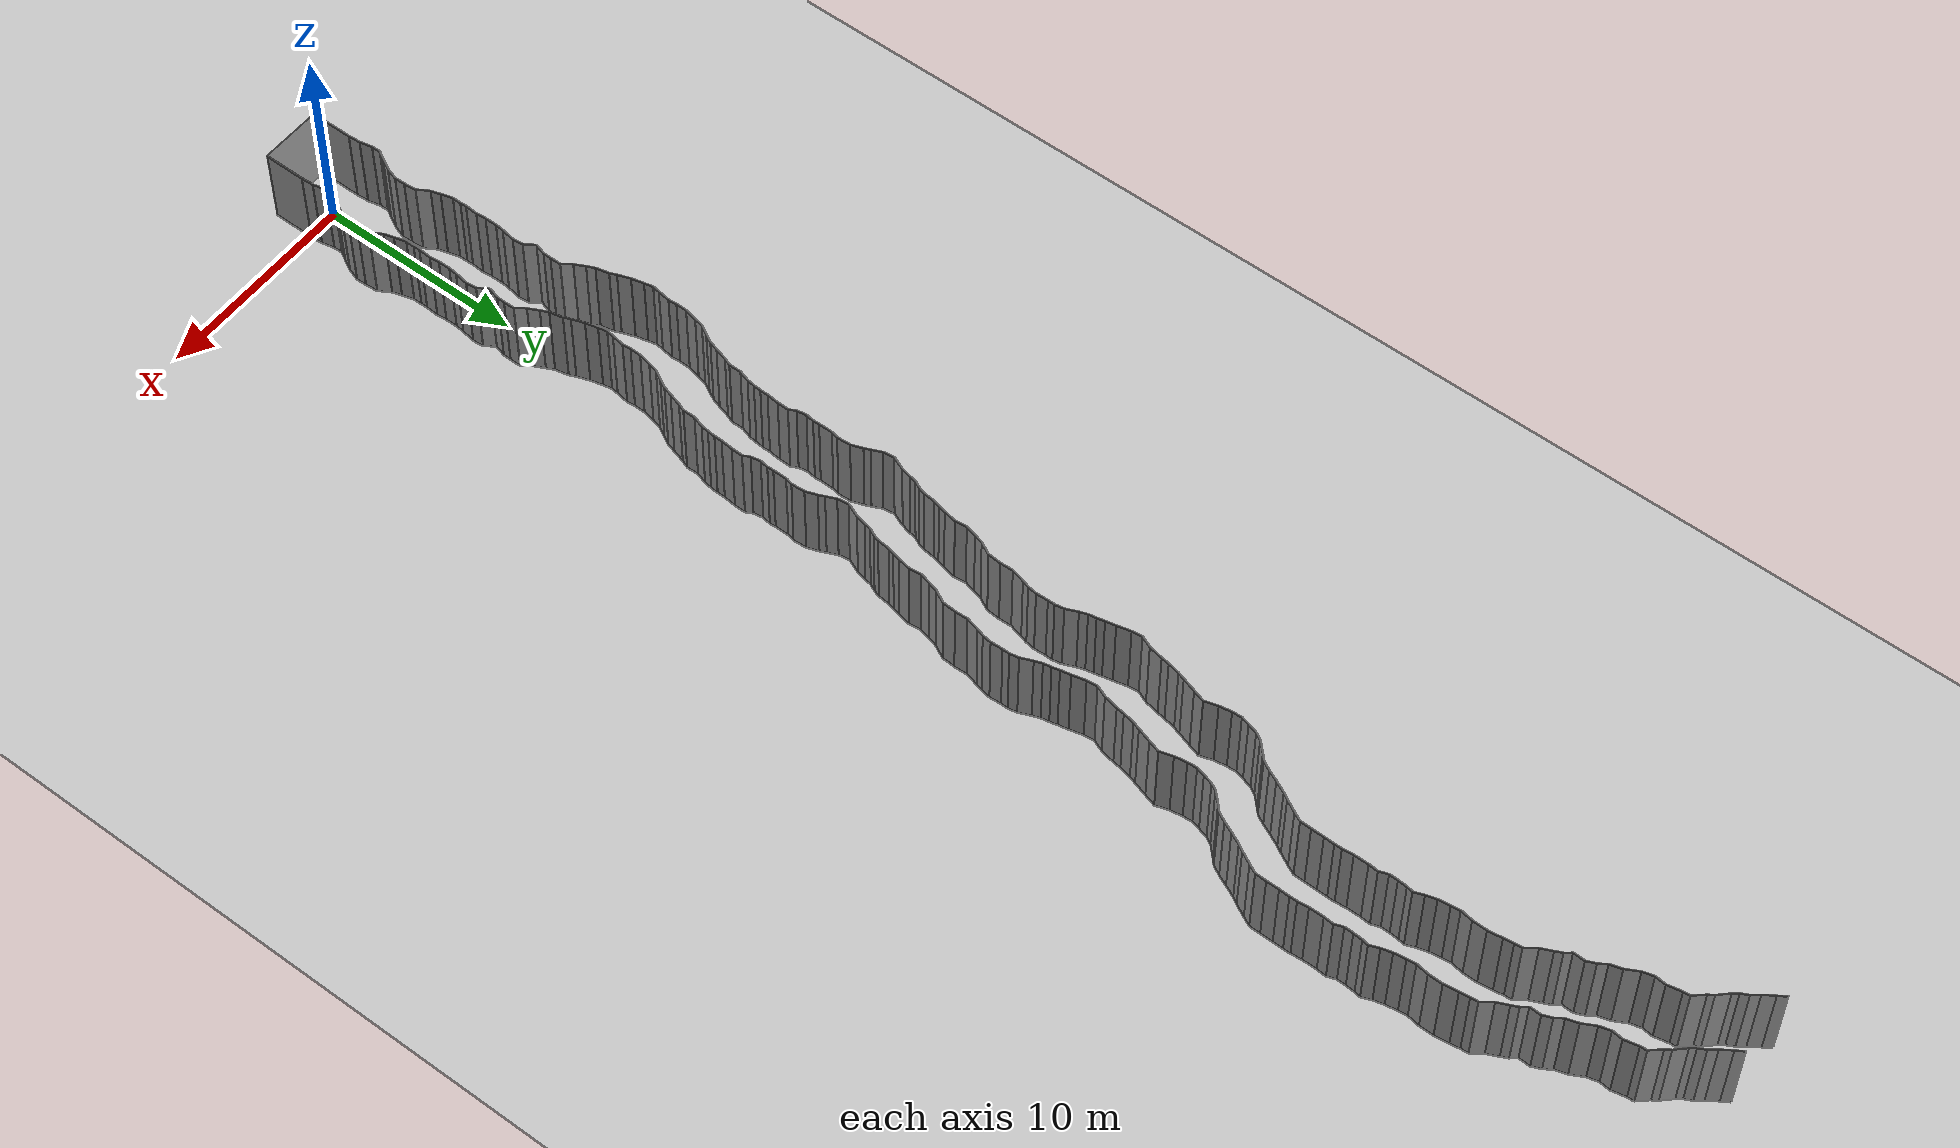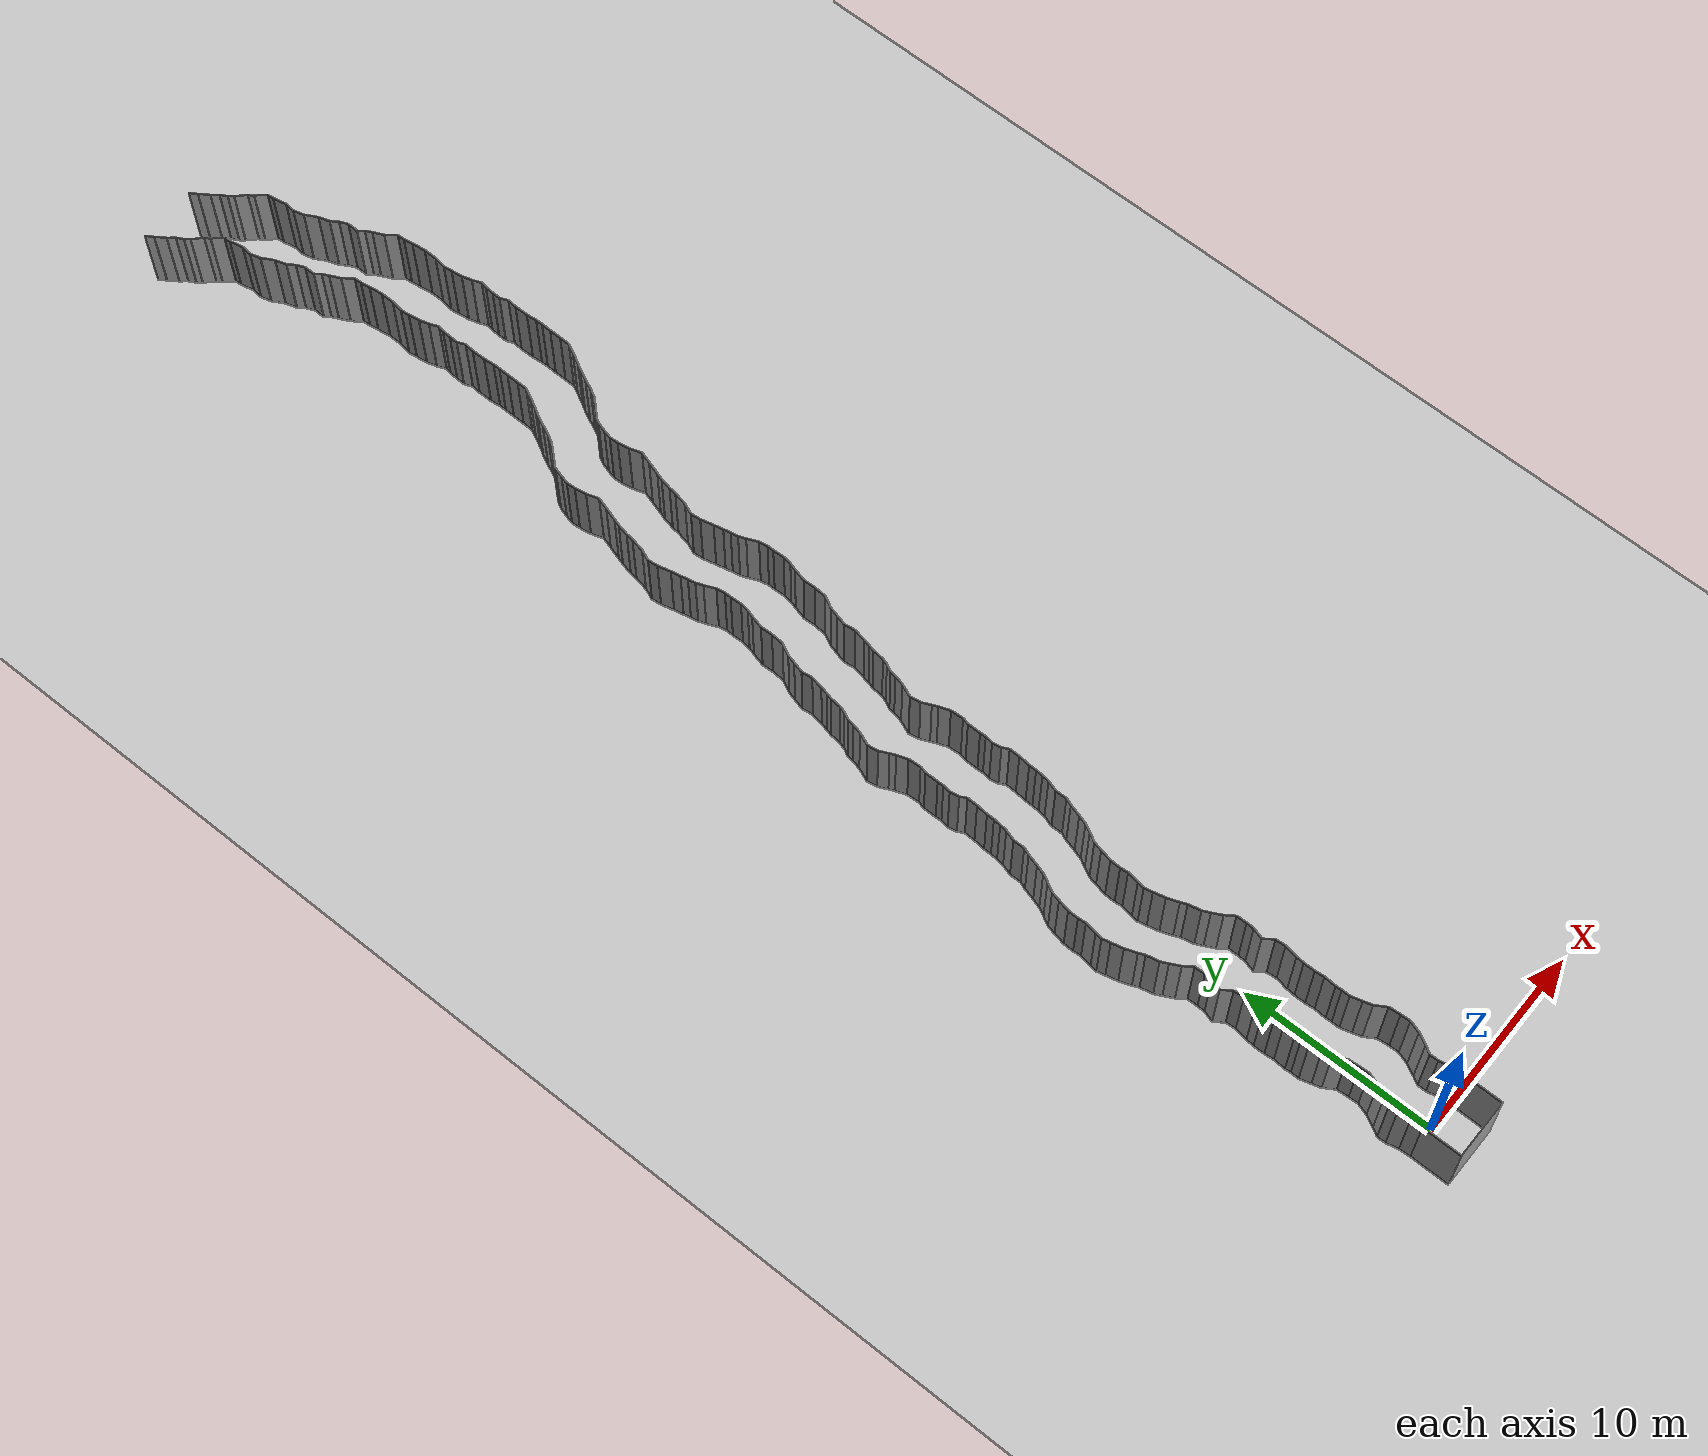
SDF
<sdf version="1.6">
 <world name="default">
  <light name="sun" type="directional">
   <pose>0 0 10 0 -0 0</pose>
   <diffuse>0.8 0.8 0.8 1</diffuse>
   <specular>0.2 0.2 0.2 1</specular>
   <attenuation>
    <range>1000</range>
    <constant>0.9</constant>
    <linear>0.01</linear>
    <quadratic>0.001</quadratic>
   </attenuation>
   <direction>-0.5 0.1 -0.9</direction>
  </light>
  <model name="ground_plane">
   <static>1</static>
   <link name="link">
    <collision name="collision">
     <geometry><plane><normal>0 0 1</normal><size>200 200</size></plane></geometry>
     <surface><friction><ode><mu>100</mu><mu2>50</mu2></ode></friction></surface>
    </collision>
    <visual name="visual">
     <cast_shadows>0</cast_shadows>
     <geometry><plane><normal>0 0 1</normal><size>200 200</size></plane></geometry>
     <material>
      <script><uri>file://media/materials/scripts/gazebo.material</uri><name>Gazebo/Grey</name></script>
     </material>
    </visual>
   </link>
   <pose>0 100 0 0 -0 0</pose>
  </model>
  <gravity>0 0 -9.8</gravity>
  <magnetic_field>6e-06 2.3e-05 -4.2e-05</magnetic_field>
  <atmosphere type="adiabatic"/>
  <physics default="0" name="default_physics" type="ode">
   <max_step_size>0.001</max_step_size>
   <real_time_factor>1</real_time_factor>
   <real_time_update_rate>1000</real_time_update_rate>
  </physics>
  <scene><ambient>0.4 0.4 0.4 1</ambient><background>0.7 0.7 0.7 1</background><shadows>1</shadows></scene>
  <spherical_coordinates>
   <surface_model>EARTH_WGS84</surface_model>
   <latitude_deg>0</latitude_deg>
   <longitude_deg>0</longitude_deg>
   <elevation>0</elevation>
   <heading_deg>0</heading_deg>
  </spherical_coordinates>
  <model name="wall_back">
   <static>1</static>
   <pose>0.0 -2 2 0.0 0 0.0</pose>
   <link name="link">
    <collision name="collision"><geometry><box><size>3 0.02 4</size></box></geometry></collision>
    <visual name="visual">
     <material>
      <script><name>Gazebo/Grey</name><uri>file://media/materials/scripts/gazebo.material</uri></script>
     </material>
     <geometry><box><size>3 0.02 4</size></box></geometry>
    </visual>
   </link>
  </model>
  <model name="wall_left">
   <static>1</static>
   <pose>1.5 -1 2 0 0 0.00</pose>
   <link name="link">
    <collision name="collision"><geometry><box><size>0.02 2 4</size></box></geometry></collision>
    <visual name="visual">
     <material>
      <script><name>Gazebo/Grey</name><uri>file://media/materials/scripts/gazebo.material</uri></script>
     </material>
     <geometry><box><size>0.02 2 4</size></box></geometry>
    </visual>
   </link>
  </model>
  <model name="wall_right">
   <static>1</static>
   <pose>-1.5 -1 2 0 0 0.00</pose>
   <link name="link">
    <collision name="collision"><geometry><box><size>0.02 2 4</size></box></geometry></collision>
    <visual name="visual">
     <material>
      <script><name>Gazebo/Grey</name><uri>file://media/materials/scripts/gazebo.material</uri></script>
     </material>
     <geometry><box><size>0.02 2 4</size></box></geometry>
    </visual>
   </link>
  </model>
  <model name="wall_0">
   <static>1</static>
   <pose>-1.5185113302899953 0.29492053365941223 2 0 0 0.06268494618193361</pose>
   <link name="link">
    <collision name="collision"><geometry><box><size>0.02 0.591001829178 4</size></box></geometry></collision>
    <visual name="visual">
     <material>
      <script><name>Gazebo/Grey</name><uri>file://media/materials/scripts/gazebo.material</uri></script>
     </material>
     <geometry><box><size>0.02 0.591001829178 4</size></box></geometry>
    </visual>
   </link>
  </model>
  <model name="wall_1">
   <static>1</static>
   <pose>1.4814886697100047 0.29492053365941223 2 0 0 0.06268494618193361</pose>
   <link name="link">
    <collision name="collision"><geometry><box><size>0.02 0.591001829178 4</size></box></geometry></collision>
    <visual name="visual">
     <material>
      <script><name>Gazebo/Grey</name><uri>file://media/materials/scripts/gazebo.material</uri></script>
     </material>
     <geometry><box><size>0.02 0.591001829178 4</size></box></geometry>
    </visual>
   </link>
  </model>
  <model name="wall_2">
   <static>1</static>
   <pose>-1.6032829919916214 0.8934209799906332 2 0 0 0.21489310873033826</pose>
   <link name="link">
    <collision name="collision"><geometry><box><size>0.02 0.621453763032 4</size></box></geometry></collision>
    <visual name="visual">
     <material>
      <script><name>Gazebo/Grey</name><uri>file://media/materials/scripts/gazebo.material</uri></script>
     </material>
     <geometry><box><size>0.02 0.621453763032 4</size></box></geometry>
    </visual>
   </link>
  </model>
  <model name="wall_3">
   <static>1</static>
   <pose>1.3967170080083786 0.8934209799906332 2 0 0 0.21489310873033826</pose>
   <link name="link">
    <collision name="collision"><geometry><box><size>0.02 0.621453763032 4</size></box></geometry></collision>
    <visual name="visual">
     <material>
      <script><name>Gazebo/Grey</name><uri>file://media/materials/scripts/gazebo.material</uri></script>
     </material>
     <geometry><box><size>0.02 0.621453763032 4</size></box></geometry>
    </visual>
   </link>
  </model>
  <model name="wall_4">
   <static>1</static>
   <pose>-1.6717699181645493 1.4165930140627472 2 0 0 0.01013933671222926</pose>
   <link name="link">
    <collision name="collision"><geometry><box><size>0.02 0.439206819188 4</size></box></geometry></collision>
    <visual name="visual">
     <material>
      <script><name>Gazebo/Grey</name><uri>file://media/materials/scripts/gazebo.material</uri></script>
     </material>
     <geometry><box><size>0.02 0.439206819188 4</size></box></geometry>
    </visual>
   </link>
  </model>
  <model name="wall_5">
   <static>1</static>
   <pose>1.3282300818354507 1.4165930140627472 2 0 0 0.01013933671222926</pose>
   <link name="link">
    <collision name="collision"><geometry><box><size>0.02 0.439206819188 4</size></box></geometry></collision>
    <visual name="visual">
     <material>
      <script><name>Gazebo/Grey</name><uri>file://media/materials/scripts/gazebo.material</uri></script>
     </material>
     <geometry><box><size>0.02 0.439206819188 4</size></box></geometry>
    </visual>
   </link>
  </model>
  <model name="wall_6">
   <static>1</static>
   <pose>-1.564483555409787 1.8261166421047403 2 0 0 -0.5230297693793418</pose>
   <link name="link">
    <collision name="collision"><geometry><box><size>0.02 0.438484047961 4</size></box></geometry></collision>
    <visual name="visual">
     <material>
      <script><name>Gazebo/Grey</name><uri>file://media/materials/scripts/gazebo.material</uri></script>
     </material>
     <geometry><box><size>0.02 0.438484047961 4</size></box></geometry>
    </visual>
   </link>
  </model>
  <model name="wall_7">
   <static>1</static>
   <pose>1.435516444590213 1.8261166421047403 2 0 0 -0.5230297693793418</pose>
   <link name="link">
    <collision name="collision"><geometry><box><size>0.02 0.438484047961 4</size></box></geometry></collision>
    <visual name="visual">
     <material>
      <script><name>Gazebo/Grey</name><uri>file://media/materials/scripts/gazebo.material</uri></script>
     </material>
     <geometry><box><size>0.02 0.438484047961 4</size></box></geometry>
    </visual>
   </link>
  </model>
  <model name="wall_8">
   <static>1</static>
   <pose>-1.3079854881451538 2.28842004208476 2 0 0 -0.494861154514529</pose>
   <link name="link">
    <collision name="collision"><geometry><box><size>0.02 0.619002651912 4</size></box></geometry></collision>
    <visual name="visual">
     <material>
      <script><name>Gazebo/Grey</name><uri>file://media/materials/scripts/gazebo.material</uri></script>
     </material>
     <geometry><box><size>0.02 0.619002651912 4</size></box></geometry>
    </visual>
   </link>
  </model>
  <model name="wall_9">
   <static>1</static>
   <pose>1.6920145118548462 2.28842004208476 2 0 0 -0.494861154514529</pose>
   <link name="link">
    <collision name="collision"><geometry><box><size>0.02 0.619002651912 4</size></box></geometry></collision>
    <visual name="visual">
     <material>
      <script><name>Gazebo/Grey</name><uri>file://media/materials/scripts/gazebo.material</uri></script>
     </material>
     <geometry><box><size>0.02 0.619002651912 4</size></box></geometry>
    </visual>
   </link>
  </model>
  <model name="wall_10">
   <static>1</static>
   <pose>-1.0661413791661865 2.85140010841985 2 0 0 -0.31551159724259165</pose>
   <link name="link">
    <collision name="collision"><geometry><box><size>0.02 0.611396237959 4</size></box></geometry></collision>
    <visual name="visual">
     <material>
      <script><name>Gazebo/Grey</name><uri>file://media/materials/scripts/gazebo.material</uri></script>
     </material>
     <geometry><box><size>0.02 0.611396237959 4</size></box></geometry>
    </visual>
   </link>
  </model>
  <model name="wall_11">
   <static>1</static>
   <pose>1.9338586208338135 2.85140010841985 2 0 0 -0.31551159724259165</pose>
   <link name="link">
    <collision name="collision"><geometry><box><size>0.02 0.611396237959 4</size></box></geometry></collision>
    <visual name="visual">
     <material>
      <script><name>Gazebo/Grey</name><uri>file://media/materials/scripts/gazebo.material</uri></script>
     </material>
     <geometry><box><size>0.02 0.611396237959 4</size></box></geometry>
    </visual>
   </link>
  </model>
  <model name="wall_12">
   <static>1</static>
   <pose>-0.9777345321164603 3.392752021765001 2 0 0 0.02572637970492103</pose>
   <link name="link">
    <collision name="collision"><geometry><box><size>0.02 0.501653480369 4</size></box></geometry></collision>
    <visual name="visual">
     <material>
      <script><name>Gazebo/Grey</name><uri>file://media/materials/scripts/gazebo.material</uri></script>
     </material>
     <geometry><box><size>0.02 0.501653480369 4</size></box></geometry>
    </visual>
   </link>
  </model>
  <model name="wall_13">
   <static>1</static>
   <pose>2.02226546788354 3.392752021765001 2 0 0 0.02572637970492103</pose>
   <link name="link">
    <collision name="collision"><geometry><box><size>0.02 0.501653480369 4</size></box></geometry></collision>
    <visual name="visual">
     <material>
      <script><name>Gazebo/Grey</name><uri>file://media/materials/scripts/gazebo.material</uri></script>
     </material>
     <geometry><box><size>0.02 0.501653480369 4</size></box></geometry>
    </visual>
   </link>
  </model>
  <model name="wall_14">
   <static>1</static>
   <pose>-1.0103047833967183 3.9452632291662355 2 0 0 0.08633526419710445</pose>
   <link name="link">
    <collision name="collision"><geometry><box><size>0.02 0.605791248772 4</size></box></geometry></collision>
    <visual name="visual">
     <material>
      <script><name>Gazebo/Grey</name><uri>file://media/materials/scripts/gazebo.material</uri></script>
     </material>
     <geometry><box><size>0.02 0.605791248772 4</size></box></geometry>
    </visual>
   </link>
  </model>
  <model name="wall_15">
   <static>1</static>
   <pose>1.9896952166032817 3.9452632291662355 2 0 0 0.08633526419710445</pose>
   <link name="link">
    <collision name="collision"><geometry><box><size>0.02 0.605791248772 4</size></box></geometry></collision>
    <visual name="visual">
     <material>
      <script><name>Gazebo/Grey</name><uri>file://media/materials/scripts/gazebo.material</uri></script>
     </material>
     <geometry><box><size>0.02 0.605791248772 4</size></box></geometry>
    </visual>
   </link>
  </model>
  <model name="wall_16">
   <static>1</static>
   <pose>-1.2070850937719821 4.525897922408958 2 0 0 0.5491845164646493</pose>
   <link name="link">
    <collision name="collision"><geometry><box><size>0.02 0.653888431463 4</size></box></geometry></collision>
    <visual name="visual">
     <material>
      <script><name>Gazebo/Grey</name><uri>file://media/materials/scripts/gazebo.material</uri></script>
     </material>
     <geometry><box><size>0.02 0.653888431463 4</size></box></geometry>
    </visual>
   </link>
  </model>
  <model name="wall_17">
   <static>1</static>
   <pose>1.7929149062280179 4.525897922408958 2 0 0 0.5491845164646493</pose>
   <link name="link">
    <collision name="collision"><geometry><box><size>0.02 0.653888431463 4</size></box></geometry></collision>
    <visual name="visual">
     <material>
      <script><name>Gazebo/Grey</name><uri>file://media/materials/scripts/gazebo.material</uri></script>
     </material>
     <geometry><box><size>0.02 0.653888431463 4</size></box></geometry>
    </visual>
   </link>
  </model>
  <model name="wall_18">
   <static>1</static>
   <pose>-1.4438042020006907 5.031598427493949 2 0 0 0.28337635448221904</pose>
   <link name="link">
    <collision name="collision"><geometry><box><size>0.02 0.472511799003 4</size></box></geometry></collision>
    <visual name="visual">
     <material>
      <script><name>Gazebo/Grey</name><uri>file://media/materials/scripts/gazebo.material</uri></script>
     </material>
     <geometry><box><size>0.02 0.472511799003 4</size></box></geometry>
    </visual>
   </link>
  </model>
  <model name="wall_19">
   <static>1</static>
   <pose>1.5561957979993093 5.031598427493949 2 0 0 0.28337635448221904</pose>
   <link name="link">
    <collision name="collision"><geometry><box><size>0.02 0.472511799003 4</size></box></geometry></collision>
    <visual name="visual">
     <material>
      <script><name>Gazebo/Grey</name><uri>file://media/materials/scripts/gazebo.material</uri></script>
     </material>
     <geometry><box><size>0.02 0.472511799003 4</size></box></geometry>
    </visual>
   </link>
  </model>
  <model name="wall_20">
   <static>1</static>
   <pose>-1.5890637419099451 5.540976157062023 2 0 0 0.2733047007655978</pose>
   <link name="link">
    <collision name="collision"><geometry><box><size>0.02 0.586871111088 4</size></box></geometry></collision>
    <visual name="visual">
     <material>
      <script><name>Gazebo/Grey</name><uri>file://media/materials/scripts/gazebo.material</uri></script>
     </material>
     <geometry><box><size>0.02 0.586871111088 4</size></box></geometry>
    </visual>
   </link>
  </model>
  <model name="wall_21">
   <static>1</static>
   <pose>1.4109362580900549 5.540976157062023 2 0 0 0.2733047007655978</pose>
   <link name="link">
    <collision name="collision"><geometry><box><size>0.02 0.586871111088 4</size></box></geometry></collision>
    <visual name="visual">
     <material>
      <script><name>Gazebo/Grey</name><uri>file://media/materials/scripts/gazebo.material</uri></script>
     </material>
     <geometry><box><size>0.02 0.586871111088 4</size></box></geometry>
    </visual>
   </link>
  </model>
  <model name="wall_22">
   <static>1</static>
   <pose>-1.6657555820865915 6.032643910130681 2 0 0 -0.012005750270716417</pose>
   <link name="link">
    <collision name="collision"><geometry><box><size>0.02 0.418276749225 4</size></box></geometry></collision>
    <visual name="visual">
     <material>
      <script><name>Gazebo/Grey</name><uri>file://media/materials/scripts/gazebo.material</uri></script>
     </material>
     <geometry><box><size>0.02 0.418276749225 4</size></box></geometry>
    </visual>
   </link>
  </model>
  <model name="wall_23">
   <static>1</static>
   <pose>1.3342444179134085 6.032643910130681 2 0 0 -0.012005750270716417</pose>
   <link name="link">
    <collision name="collision"><geometry><box><size>0.02 0.418276749225 4</size></box></geometry></collision>
    <visual name="visual">
     <material>
      <script><name>Gazebo/Grey</name><uri>file://media/materials/scripts/gazebo.material</uri></script>
     </material>
     <geometry><box><size>0.02 0.418276749225 4</size></box></geometry>
    </visual>
   </link>
  </model>
  <model name="wall_24">
   <static>1</static>
   <pose>-1.673975837094244 6.395071165094762 2 0 0 0.06988458076299657</pose>
   <link name="link">
    <collision name="collision"><geometry><box><size>0.02 0.307358145975 4</size></box></geometry></collision>
    <visual name="visual">
     <material>
      <script><name>Gazebo/Grey</name><uri>file://media/materials/scripts/gazebo.material</uri></script>
     </material>
     <geometry><box><size>0.02 0.307358145975 4</size></box></geometry>
    </visual>
   </link>
  </model>
  <model name="wall_25">
   <static>1</static>
   <pose>1.326024162905756 6.395071165094762 2 0 0 0.06988458076299657</pose>
   <link name="link">
    <collision name="collision"><geometry><box><size>0.02 0.307358145975 4</size></box></geometry></collision>
    <visual name="visual">
     <material>
      <script><name>Gazebo/Grey</name><uri>file://media/materials/scripts/gazebo.material</uri></script>
     </material>
     <geometry><box><size>0.02 0.307358145975 4</size></box></geometry>
    </visual>
   </link>
  </model>
  <model name="wall_26">
   <static>1</static>
   <pose>-1.6623951007712896 6.860203549148598 2 0 0 -0.07142977496817592</pose>
   <link name="link">
    <collision name="collision"><geometry><box><size>0.02 0.625251267377 4</size></box></geometry></collision>
    <visual name="visual">
     <material>
      <script><name>Gazebo/Grey</name><uri>file://media/materials/scripts/gazebo.material</uri></script>
     </material>
     <geometry><box><size>0.02 0.625251267377 4</size></box></geometry>
    </visual>
   </link>
  </model>
  <model name="wall_27">
   <static>1</static>
   <pose>1.3376048992287104 6.860203549148598 2 0 0 -0.07142977496817592</pose>
   <link name="link">
    <collision name="collision"><geometry><box><size>0.02 0.625251267377 4</size></box></geometry></collision>
    <visual name="visual">
     <material>
      <script><name>Gazebo/Grey</name><uri>file://media/materials/scripts/gazebo.material</uri></script>
     </material>
     <geometry><box><size>0.02 0.625251267377 4</size></box></geometry>
    </visual>
   </link>
  </model>
  <model name="wall_28">
   <static>1</static>
   <pose>-1.663334344448311 7.41137713941059 2 0 0 0.09684051691092106</pose>
   <link name="link">
    <collision name="collision"><geometry><box><size>0.02 0.480943721398 4</size></box></geometry></collision>
    <visual name="visual">
     <material>
      <script><name>Gazebo/Grey</name><uri>file://media/materials/scripts/gazebo.material</uri></script>
     </material>
     <geometry><box><size>0.02 0.480943721398 4</size></box></geometry>
    </visual>
   </link>
  </model>
  <model name="wall_29">
   <static>1</static>
   <pose>1.336665655551689 7.41137713941059 2 0 0 0.09684051691092106</pose>
   <link name="link">
    <collision name="collision"><geometry><box><size>0.02 0.480943721398 4</size></box></geometry></collision>
    <visual name="visual">
     <material>
      <script><name>Gazebo/Grey</name><uri>file://media/materials/scripts/gazebo.material</uri></script>
     </material>
     <geometry><box><size>0.02 0.480943721398 4</size></box></geometry>
    </visual>
   </link>
  </model>
  <model name="wall_30">
   <static>1</static>
   <pose>-1.6903792075558648 7.939358403514229 2 0 0 0.013143216645869699</pose>
   <link name="link">
    <collision name="collision"><geometry><box><size>0.02 0.57732207444 4</size></box></geometry></collision>
    <visual name="visual">
     <material>
      <script><name>Gazebo/Grey</name><uri>file://media/materials/scripts/gazebo.material</uri></script>
     </material>
     <geometry><box><size>0.02 0.57732207444 4</size></box></geometry>
    </visual>
   </link>
  </model>
  <model name="wall_31">
   <static>1</static>
   <pose>1.3096207924441352 7.939358403514229 2 0 0 0.013143216645869699</pose>
   <link name="link">
    <collision name="collision"><geometry><box><size>0.02 0.57732207444 4</size></box></geometry></collision>
    <visual name="visual">
     <material>
      <script><name>Gazebo/Grey</name><uri>file://media/materials/scripts/gazebo.material</uri></script>
     </material>
     <geometry><box><size>0.02 0.57732207444 4</size></box></geometry>
    </visual>
   </link>
  </model>
  <model name="wall_32">
   <static>1</static>
   <pose>-1.6734789334931783 8.435392126474458 2 0 0 -0.09945065932975414</pose>
   <link name="link">
    <collision name="collision"><geometry><box><size>0.02 0.416854975017 4</size></box></geometry></collision>
    <visual name="visual">
     <material>
      <script><name>Gazebo/Grey</name><uri>file://media/materials/scripts/gazebo.material</uri></script>
     </material>
     <geometry><box><size>0.02 0.416854975017 4</size></box></geometry>
    </visual>
   </link>
  </model>
  <model name="wall_33">
   <static>1</static>
   <pose>1.3265210665068217 8.435392126474458 2 0 0 -0.09945065932975414</pose>
   <link name="link">
    <collision name="collision"><geometry><box><size>0.02 0.416854975017 4</size></box></geometry></collision>
    <visual name="visual">
     <material>
      <script><name>Gazebo/Grey</name><uri>file://media/materials/scripts/gazebo.material</uri></script>
     </material>
     <geometry><box><size>0.02 0.416854975017 4</size></box></geometry>
    </visual>
   </link>
  </model>
  <model name="wall_34">
   <static>1</static>
   <pose>-1.5974431035443908 8.97267009533746 2 0 0 -0.16621522903037272</pose>
   <link name="link">
    <collision name="collision"><geometry><box><size>0.02 0.668980577504 4</size></box></geometry></collision>
    <visual name="visual">
     <material>
      <script><name>Gazebo/Grey</name><uri>file://media/materials/scripts/gazebo.material</uri></script>
     </material>
     <geometry><box><size>0.02 0.668980577504 4</size></box></geometry>
    </visual>
   </link>
  </model>
  <model name="wall_35">
   <static>1</static>
   <pose>1.4025568964556092 8.97267009533746 2 0 0 -0.16621522903037272</pose>
   <link name="link">
    <collision name="collision"><geometry><box><size>0.02 0.668980577504 4</size></box></geometry></collision>
    <visual name="visual">
     <material>
      <script><name>Gazebo/Grey</name><uri>file://media/materials/scripts/gazebo.material</uri></script>
     </material>
     <geometry><box><size>0.02 0.668980577504 4</size></box></geometry>
    </visual>
   </link>
  </model>
  <model name="wall_36">
   <static>1</static>
   <pose>-1.5653315406791224 9.559392271478405 2 0 0 0.09020000143591118</pose>
   <link name="link">
    <collision name="collision"><geometry><box><size>0.02 0.515780432801 4</size></box></geometry></collision>
    <visual name="visual">
     <material>
      <script><name>Gazebo/Grey</name><uri>file://media/materials/scripts/gazebo.material</uri></script>
     </material>
     <geometry><box><size>0.02 0.515780432801 4</size></box></geometry>
    </visual>
   </link>
  </model>
  <model name="wall_37">
   <static>1</static>
   <pose>1.4346684593208776 9.559392271478405 2 0 0 0.09020000143591118</pose>
   <link name="link">
    <collision name="collision"><geometry><box><size>0.02 0.515780432801 4</size></box></geometry></collision>
    <visual name="visual">
     <material>
      <script><name>Gazebo/Grey</name><uri>file://media/materials/scripts/gazebo.material</uri></script>
     </material>
     <geometry><box><size>0.02 0.515780432801 4</size></box></geometry>
    </visual>
   </link>
  </model>
  <model name="wall_38">
   <static>1</static>
   <pose>-1.755232263156484 10.061373956086669 2 0 0 0.5971081742099745</pose>
   <link name="link">
    <collision name="collision"><geometry><box><size>0.02 0.592866341234 4</size></box></geometry></collision>
    <visual name="visual">
     <material>
      <script><name>Gazebo/Grey</name><uri>file://media/materials/scripts/gazebo.material</uri></script>
     </material>
     <geometry><box><size>0.02 0.592866341234 4</size></box></geometry>
    </visual>
   </link>
  </model>
  <model name="wall_39">
   <static>1</static>
   <pose>1.244767736843516 10.061373956086669 2 0 0 0.5971081742099745</pose>
   <link name="link">
    <collision name="collision"><geometry><box><size>0.02 0.592866341234 4</size></box></geometry></collision>
    <visual name="visual">
     <material>
      <script><name>Gazebo/Grey</name><uri>file://media/materials/scripts/gazebo.material</uri></script>
     </material>
     <geometry><box><size>0.02 0.592866341234 4</size></box></geometry>
    </visual>
   </link>
  </model>
  <model name="wall_40">
   <static>1</static>
   <pose>-1.8415697863617506 10.573384954875786 2 0 0 -0.29239052917902836</pose>
   <link name="link">
    <collision name="collision"><geometry><box><size>0.02 0.557399680092 4</size></box></geometry></collision>
    <visual name="visual">
     <material>
      <script><name>Gazebo/Grey</name><uri>file://media/materials/scripts/gazebo.material</uri></script>
     </material>
     <geometry><box><size>0.02 0.557399680092 4</size></box></geometry>
    </visual>
   </link>
  </model>
  <model name="wall_41">
   <static>1</static>
   <pose>1.1584302136382494 10.573384954875786 2 0 0 -0.29239052917902836</pose>
   <link name="link">
    <collision name="collision"><geometry><box><size>0.02 0.557399680092 4</size></box></geometry></collision>
    <visual name="visual">
     <material>
      <script><name>Gazebo/Grey</name><uri>file://media/materials/scripts/gazebo.material</uri></script>
     </material>
     <geometry><box><size>0.02 0.557399680092 4</size></box></geometry>
    </visual>
   </link>
  </model>
  <model name="wall_42">
   <static>1</static>
   <pose>-1.7560762919183144 11.035589577510985 2 0 0 -0.026412587847882592</pose>
   <link name="link">
    <collision name="collision"><geometry><box><size>0.02 0.39080327619 4</size></box></geometry></collision>
    <visual name="visual">
     <material>
      <script><name>Gazebo/Grey</name><uri>file://media/materials/scripts/gazebo.material</uri></script>
     </material>
     <geometry><box><size>0.02 0.39080327619 4</size></box></geometry>
    </visual>
   </link>
  </model>
  <model name="wall_43">
   <static>1</static>
   <pose>1.2439237080816856 11.035589577510985 2 0 0 -0.026412587847882592</pose>
   <link name="link">
    <collision name="collision"><geometry><box><size>0.02 0.39080327619 4</size></box></geometry></collision>
    <visual name="visual">
     <material>
      <script><name>Gazebo/Grey</name><uri>file://media/materials/scripts/gazebo.material</uri></script>
     </material>
     <geometry><box><size>0.02 0.39080327619 4</size></box></geometry>
    </visual>
   </link>
  </model>
  <model name="wall_44">
   <static>1</static>
   <pose>-1.7538173183699357 11.498250930627945 2 0 0 0.010853246996506407</pose>
   <link name="link">
    <collision name="collision"><geometry><box><size>0.02 0.534687230037 4</size></box></geometry></collision>
    <visual name="visual">
     <material>
      <script><name>Gazebo/Grey</name><uri>file://media/materials/scripts/gazebo.material</uri></script>
     </material>
     <geometry><box><size>0.02 0.534687230037 4</size></box></geometry>
    </visual>
   </link>
  </model>
  <model name="wall_45">
   <static>1</static>
   <pose>1.2461826816300643 11.498250930627945 2 0 0 0.010853246996506407</pose>
   <link name="link">
    <collision name="collision"><geometry><box><size>0.02 0.534687230037 4</size></box></geometry></collision>
    <visual name="visual">
     <material>
      <script><name>Gazebo/Grey</name><uri>file://media/materials/scripts/gazebo.material</uri></script>
     </material>
     <geometry><box><size>0.02 0.534687230037 4</size></box></geometry>
    </visual>
   </link>
  </model>
  <model name="wall_46">
   <static>1</static>
   <pose>-1.919704327145059 11.989113639711922 2 0 0 0.6300086907917413</pose>
   <link name="link">
    <collision name="collision"><geometry><box><size>0.02 0.553288727613 4</size></box></geometry></collision>
    <visual name="visual">
     <material>
      <script><name>Gazebo/Grey</name><uri>file://media/materials/scripts/gazebo.material</uri></script>
     </material>
     <geometry><box><size>0.02 0.553288727613 4</size></box></geometry>
    </visual>
   </link>
  </model>
  <model name="wall_47">
   <static>1</static>
   <pose>1.080295672854941 11.989113639711922 2 0 0 0.6300086907917413</pose>
   <link name="link">
    <collision name="collision"><geometry><box><size>0.02 0.553288727613 4</size></box></geometry></collision>
    <visual name="visual">
     <material>
      <script><name>Gazebo/Grey</name><uri>file://media/materials/scripts/gazebo.material</uri></script>
     </material>
     <geometry><box><size>0.02 0.553288727613 4</size></box></geometry>
    </visual>
   </link>
  </model>
  <model name="wall_48">
   <static>1</static>
   <pose>-2.208310492446414 12.460964968108582 2 0 0 0.4683479131257227</pose>
   <link name="link">
    <collision name="collision"><geometry><box><size>0.02 0.55656670873 4</size></box></geometry></collision>
    <visual name="visual">
     <material>
      <script><name>Gazebo/Grey</name><uri>file://media/materials/scripts/gazebo.material</uri></script>
     </material>
     <geometry><box><size>0.02 0.55656670873 4</size></box></geometry>
    </visual>
   </link>
  </model>
  <model name="wall_49">
   <static>1</static>
   <pose>0.7916895075535861 12.460964968108582 2 0 0 0.4683479131257227</pose>
   <link name="link">
    <collision name="collision"><geometry><box><size>0.02 0.55656670873 4</size></box></geometry></collision>
    <visual name="visual">
     <material>
      <script><name>Gazebo/Grey</name><uri>file://media/materials/scripts/gazebo.material</uri></script>
     </material>
     <geometry><box><size>0.02 0.55656670873 4</size></box></geometry>
    </visual>
   </link>
  </model>
  <model name="wall_50">
   <static>1</static>
   <pose>-2.422641076564206 12.894296970132887 2 0 0 0.4470915497425742</pose>
   <link name="link">
    <collision name="collision"><geometry><box><size>0.02 0.410366632412 4</size></box></geometry></collision>
    <visual name="visual">
     <material>
      <script><name>Gazebo/Grey</name><uri>file://media/materials/scripts/gazebo.material</uri></script>
     </material>
     <geometry><box><size>0.02 0.410366632412 4</size></box></geometry>
    </visual>
   </link>
  </model>
  <model name="wall_51">
   <static>1</static>
   <pose>0.5773589234357939 12.894296970132887 2 0 0 0.4470915497425742</pose>
   <link name="link">
    <collision name="collision"><geometry><box><size>0.02 0.410366632412 4</size></box></geometry></collision>
    <visual name="visual">
     <material>
      <script><name>Gazebo/Grey</name><uri>file://media/materials/scripts/gazebo.material</uri></script>
     </material>
     <geometry><box><size>0.02 0.410366632412 4</size></box></geometry>
    </visual>
   </link>
  </model>
  <model name="wall_52">
   <static>1</static>
   <pose>-2.581965683001096 13.399046261598889 2 0 0 0.21736528301390892</pose>
   <link name="link">
    <collision name="collision"><geometry><box><size>0.02 0.654877455298 4</size></box></geometry></collision>
    <visual name="visual">
     <material>
      <script><name>Gazebo/Grey</name><uri>file://media/materials/scripts/gazebo.material</uri></script>
     </material>
     <geometry><box><size>0.02 0.654877455298 4</size></box></geometry>
    </visual>
   </link>
  </model>
  <model name="wall_53">
   <static>1</static>
   <pose>0.41803431699890403 13.399046261598889 2 0 0 0.21736528301390892</pose>
   <link name="link">
    <collision name="collision"><geometry><box><size>0.02 0.654877455298 4</size></box></geometry></collision>
    <visual name="visual">
     <material>
      <script><name>Gazebo/Grey</name><uri>file://media/materials/scripts/gazebo.material</uri></script>
     </material>
     <geometry><box><size>0.02 0.654877455298 4</size></box></geometry>
    </visual>
   </link>
  </model>
  <model name="wall_54">
   <static>1</static>
   <pose>-2.719855267819281 13.877838774071202 2 0 0 0.4001384649570777</pose>
   <link name="link">
    <collision name="collision"><geometry><box><size>0.02 0.345401767904 4</size></box></geometry></collision>
    <visual name="visual">
     <material>
      <script><name>Gazebo/Grey</name><uri>file://media/materials/scripts/gazebo.material</uri></script>
     </material>
     <geometry><box><size>0.02 0.345401767904 4</size></box></geometry>
    </visual>
   </link>
  </model>
  <model name="wall_55">
   <static>1</static>
   <pose>0.2801447321807191 13.877838774071202 2 0 0 0.4001384649570777</pose>
   <link name="link">
    <collision name="collision"><geometry><box><size>0.02 0.345401767904 4</size></box></geometry></collision>
    <visual name="visual">
     <material>
      <script><name>Gazebo/Grey</name><uri>file://media/materials/scripts/gazebo.material</uri></script>
     </material>
     <geometry><box><size>0.02 0.345401767904 4</size></box></geometry>
    </visual>
   </link>
  </model>
  <model name="wall_56">
   <static>1</static>
   <pose>-2.894246697715273 14.333794653706013 2 0 0 0.34625176333253266</pose>
   <link name="link">
    <collision name="collision"><geometry><box><size>0.02 0.63125862342 4</size></box></geometry></collision>
    <visual name="visual">
     <material>
      <script><name>Gazebo/Grey</name><uri>file://media/materials/scripts/gazebo.material</uri></script>
     </material>
     <geometry><box><size>0.02 0.63125862342 4</size></box></geometry>
    </visual>
   </link>
  </model>
  <model name="wall_57">
   <static>1</static>
   <pose>0.10575330228472701 14.333794653706013 2 0 0 0.34625176333253266</pose>
   <link name="link">
    <collision name="collision"><geometry><box><size>0.02 0.63125862342 4</size></box></geometry></collision>
    <visual name="visual">
     <material>
      <script><name>Gazebo/Grey</name><uri>file://media/materials/scripts/gazebo.material</uri></script>
     </material>
     <geometry><box><size>0.02 0.63125862342 4</size></box></geometry>
    </visual>
   </link>
  </model>
  <model name="wall_58">
   <static>1</static>
   <pose>-3.0720271532514403 14.928912579485683 2 0 0 0.23266078091612422</pose>
   <link name="link">
    <collision name="collision"><geometry><box><size>0.02 0.612956855043 4</size></box></geometry></collision>
    <visual name="visual">
     <material>
      <script><name>Gazebo/Grey</name><uri>file://media/materials/scripts/gazebo.material</uri></script>
     </material>
     <geometry><box><size>0.02 0.612956855043 4</size></box></geometry>
    </visual>
   </link>
  </model>
  <model name="wall_59">
   <static>1</static>
   <pose>-0.07202715325144027 14.928912579485683 2 0 0 0.23266078091612422</pose>
   <link name="link">
    <collision name="collision"><geometry><box><size>0.02 0.612956855043 4</size></box></geometry></collision>
    <visual name="visual">
     <material>
      <script><name>Gazebo/Grey</name><uri>file://media/materials/scripts/gazebo.material</uri></script>
     </material>
     <geometry><box><size>0.02 0.612956855043 4</size></box></geometry>
    </visual>
   </link>
  </model>
  <model name="wall_60">
   <static>1</static>
   <pose>-3.1908167746002554 15.440115685265646 2 0 0 0.22222885732073538</pose>
   <link name="link">
    <collision name="collision"><geometry><box><size>0.02 0.43670379873 4</size></box></geometry></collision>
    <visual name="visual">
     <material>
      <script><name>Gazebo/Grey</name><uri>file://media/materials/scripts/gazebo.material</uri></script>
     </material>
     <geometry><box><size>0.02 0.43670379873 4</size></box></geometry>
    </visual>
   </link>
  </model>
  <model name="wall_61">
   <static>1</static>
   <pose>-0.19081677460025537 15.440115685265646 2 0 0 0.22222885732073538</pose>
   <link name="link">
    <collision name="collision"><geometry><box><size>0.02 0.43670379873 4</size></box></geometry></collision>
    <visual name="visual">
     <material>
      <script><name>Gazebo/Grey</name><uri>file://media/materials/scripts/gazebo.material</uri></script>
     </material>
     <geometry><box><size>0.02 0.43670379873 4</size></box></geometry>
    </visual>
   </link>
  </model>
  <model name="wall_62">
   <static>1</static>
   <pose>-3.2113391722653755 15.830278466206284 2 0 0 -0.15454953704472477</pose>
   <link name="link">
    <collision name="collision"><geometry><box><size>0.02 0.358635497056 4</size></box></geometry></collision>
    <visual name="visual">
     <material>
      <script><name>Gazebo/Grey</name><uri>file://media/materials/scripts/gazebo.material</uri></script>
     </material>
     <geometry><box><size>0.02 0.358635497056 4</size></box></geometry>
    </visual>
   </link>
  </model>
  <model name="wall_63">
   <static>1</static>
   <pose>-0.21133917226537546 15.830278466206284 2 0 0 -0.15454953704472477</pose>
   <link name="link">
    <collision name="collision"><geometry><box><size>0.02 0.358635497056 4</size></box></geometry></collision>
    <visual name="visual">
     <material>
      <script><name>Gazebo/Grey</name><uri>file://media/materials/scripts/gazebo.material</uri></script>
     </material>
     <geometry><box><size>0.02 0.358635497056 4</size></box></geometry>
    </visual>
   </link>
  </model>
  <model name="wall_64">
   <static>1</static>
   <pose>-3.1394372593649806 16.306207406749902 2 0 0 -0.14720804821156833</pose>
   <link name="link">
    <collision name="collision"><geometry><box><size>0.02 0.604029887006 4</size></box></geometry></collision>
    <visual name="visual">
     <material>
      <script><name>Gazebo/Grey</name><uri>file://media/materials/scripts/gazebo.material</uri></script>
     </material>
     <geometry><box><size>0.02 0.604029887006 4</size></box></geometry>
    </visual>
   </link>
  </model>
  <model name="wall_65">
   <static>1</static>
   <pose>-0.13943725936498064 16.306207406749902 2 0 0 -0.14720804821156833</pose>
   <link name="link">
    <collision name="collision"><geometry><box><size>0.02 0.604029887006 4</size></box></geometry></collision>
    <visual name="visual">
     <material>
      <script><name>Gazebo/Grey</name><uri>file://media/materials/scripts/gazebo.material</uri></script>
     </material>
     <geometry><box><size>0.02 0.604029887006 4</size></box></geometry>
    </visual>
   </link>
  </model>
  <model name="wall_66">
   <static>1</static>
   <pose>-3.1146367073302277 16.80770840488149 2 0 0 0.09587207561579213</pose>
   <link name="link">
    <collision name="collision"><geometry><box><size>0.02 0.407375780557 4</size></box></geometry></collision>
    <visual name="visual">
     <material>
      <script><name>Gazebo/Grey</name><uri>file://media/materials/scripts/gazebo.material</uri></script>
     </material>
     <geometry><box><size>0.02 0.407375780557 4</size></box></geometry>
    </visual>
   </link>
  </model>
  <model name="wall_67">
   <static>1</static>
   <pose>-0.11463670733022768 16.80770840488149 2 0 0 0.09587207561579213</pose>
   <link name="link">
    <collision name="collision"><geometry><box><size>0.02 0.407375780557 4</size></box></geometry></collision>
    <visual name="visual">
     <material>
      <script><name>Gazebo/Grey</name><uri>file://media/materials/scripts/gazebo.material</uri></script>
     </material>
     <geometry><box><size>0.02 0.407375780557 4</size></box></geometry>
    </visual>
   </link>
  </model>
  <model name="wall_68">
   <static>1</static>
   <pose>-3.127381730957775 17.28029139107389 2 0 0 -0.02502180855981599</pose>
   <link name="link">
    <collision name="collision"><geometry><box><size>0.02 0.539829928796 4</size></box></geometry></collision>
    <visual name="visual">
     <material>
      <script><name>Gazebo/Grey</name><uri>file://media/materials/scripts/gazebo.material</uri></script>
     </material>
     <geometry><box><size>0.02 0.539829928796 4</size></box></geometry>
    </visual>
   </link>
  </model>
  <model name="wall_69">
   <static>1</static>
   <pose>-0.12738173095777494 17.28029139107389 2 0 0 -0.02502180855981599</pose>
   <link name="link">
    <collision name="collision"><geometry><box><size>0.02 0.539829928796 4</size></box></geometry></collision>
    <visual name="visual">
     <material>
      <script><name>Gazebo/Grey</name><uri>file://media/materials/scripts/gazebo.material</uri></script>
     </material>
     <geometry><box><size>0.02 0.539829928796 4</size></box></geometry>
    </visual>
   </link>
  </model>
  <model name="wall_70">
   <static>1</static>
   <pose>-3.0596355731426916 17.846945582226983 2 0 0 -0.20266489833488943</pose>
   <link name="link">
    <collision name="collision"><geometry><box><size>0.02 0.606051080535 4</size></box></geometry></collision>
    <visual name="visual">
     <material>
      <script><name>Gazebo/Grey</name><uri>file://media/materials/scripts/gazebo.material</uri></script>
     </material>
     <geometry><box><size>0.02 0.606051080535 4</size></box></geometry>
    </visual>
   </link>
  </model>
  <model name="wall_71">
   <static>1</static>
   <pose>-0.059635573142691634 17.846945582226983 2 0 0 -0.20266489833488943</pose>
   <link name="link">
    <collision name="collision"><geometry><box><size>0.02 0.606051080535 4</size></box></geometry></collision>
    <visual name="visual">
     <material>
      <script><name>Gazebo/Grey</name><uri>file://media/materials/scripts/gazebo.material</uri></script>
     </material>
     <geometry><box><size>0.02 0.606051080535 4</size></box></geometry>
    </visual>
   </link>
  </model>
  <model name="wall_72">
   <static>1</static>
   <pose>-2.9493742182097082 18.367264299910254 2 0 0 -0.21697428535780522</pose>
   <link name="link">
    <collision name="collision"><geometry><box><size>0.02 0.457722080018 4</size></box></geometry></collision>
    <visual name="visual">
     <material>
      <script><name>Gazebo/Grey</name><uri>file://media/materials/scripts/gazebo.material</uri></script>
     </material>
     <geometry><box><size>0.02 0.457722080018 4</size></box></geometry>
    </visual>
   </link>
  </model>
  <model name="wall_73">
   <static>1</static>
   <pose>0.05062578179029176 18.367264299910254 2 0 0 -0.21697428535780522</pose>
   <link name="link">
    <collision name="collision"><geometry><box><size>0.02 0.457722080018 4</size></box></geometry></collision>
    <visual name="visual">
     <material>
      <script><name>Gazebo/Grey</name><uri>file://media/materials/scripts/gazebo.material</uri></script>
     </material>
     <geometry><box><size>0.02 0.457722080018 4</size></box></geometry>
    </visual>
   </link>
  </model>
  <model name="wall_74">
   <static>1</static>
   <pose>-2.7761507131425014 18.811209994044134 2 0 0 -0.5122231350425008</pose>
   <link name="link">
    <collision name="collision"><geometry><box><size>0.02 0.505819782957 4</size></box></geometry></collision>
    <visual name="visual">
     <material>
      <script><name>Gazebo/Grey</name><uri>file://media/materials/scripts/gazebo.material</uri></script>
     </material>
     <geometry><box><size>0.02 0.505819782957 4</size></box></geometry>
    </visual>
   </link>
  </model>
  <model name="wall_75">
   <static>1</static>
   <pose>0.2238492868574986 18.811209994044134 2 0 0 -0.5122231350425008</pose>
   <link name="link">
    <collision name="collision"><geometry><box><size>0.02 0.505819782957 4</size></box></geometry></collision>
    <visual name="visual">
     <material>
      <script><name>Gazebo/Grey</name><uri>file://media/materials/scripts/gazebo.material</uri></script>
     </material>
     <geometry><box><size>0.02 0.505819782957 4</size></box></geometry>
    </visual>
   </link>
  </model>
  <model name="wall_76">
   <static>1</static>
   <pose>-2.5505779902444363 19.226476235001357 2 0 0 -0.4807846990182478</pose>
   <link name="link">
    <collision name="collision"><geometry><box><size>0.02 0.439450600325 4</size></box></geometry></collision>
    <visual name="visual">
     <material>
      <script><name>Gazebo/Grey</name><uri>file://media/materials/scripts/gazebo.material</uri></script>
     </material>
     <geometry><box><size>0.02 0.439450600325 4</size></box></geometry>
    </visual>
   </link>
  </model>
  <model name="wall_77">
   <static>1</static>
   <pose>0.4494220097555637 19.226476235001357 2 0 0 -0.4807846990182478</pose>
   <link name="link">
    <collision name="collision"><geometry><box><size>0.02 0.439450600325 4</size></box></geometry></collision>
    <visual name="visual">
     <material>
      <script><name>Gazebo/Grey</name><uri>file://media/materials/scripts/gazebo.material</uri></script>
     </material>
     <geometry><box><size>0.02 0.439450600325 4</size></box></geometry>
    </visual>
   </link>
  </model>
  <model name="wall_78">
   <static>1</static>
   <pose>-2.3783481457230153 19.646231125166302 2 0 0 -0.3041756428201957</pose>
   <link name="link">
    <collision name="collision"><geometry><box><size>0.02 0.471524402967 4</size></box></geometry></collision>
    <visual name="visual">
     <material>
      <script><name>Gazebo/Grey</name><uri>file://media/materials/scripts/gazebo.material</uri></script>
     </material>
     <geometry><box><size>0.02 0.471524402967 4</size></box></geometry>
    </visual>
   </link>
  </model>
  <model name="wall_79">
   <static>1</static>
   <pose>0.6216518542769847 19.646231125166302 2 0 0 -0.3041756428201957</pose>
   <link name="link">
    <collision name="collision"><geometry><box><size>0.02 0.471524402967 4</size></box></geometry></collision>
    <visual name="visual">
     <material>
      <script><name>Gazebo/Grey</name><uri>file://media/materials/scripts/gazebo.material</uri></script>
     </material>
     <geometry><box><size>0.02 0.471524402967 4</size></box></geometry>
    </visual>
   </link>
  </model>
  <model name="wall_80">
   <static>1</static>
   <pose>-2.2291160718274656 20.16350314075019 2 0 0 -0.26272280154588906</pose>
   <link name="link">
    <collision name="collision"><geometry><box><size>0.02 0.605440164939 4</size></box></geometry></collision>
    <visual name="visual">
     <material>
      <script><name>Gazebo/Grey</name><uri>file://media/materials/scripts/gazebo.material</uri></script>
     </material>
     <geometry><box><size>0.02 0.605440164939 4</size></box></geometry>
    </visual>
   </link>
  </model>
  <model name="wall_81">
   <static>1</static>
   <pose>0.7708839281725344 20.16350314075019 2 0 0 -0.26272280154588906</pose>
   <link name="link">
    <collision name="collision"><geometry><box><size>0.02 0.605440164939 4</size></box></geometry></collision>
    <visual name="visual">
     <material>
      <script><name>Gazebo/Grey</name><uri>file://media/materials/scripts/gazebo.material</uri></script>
     </material>
     <geometry><box><size>0.02 0.605440164939 4</size></box></geometry>
    </visual>
   </link>
  </model>
  <model name="wall_82">
   <static>1</static>
   <pose>-2.082440634498089 20.629005949248484 2 0 0 -0.3744567340809167</pose>
   <link name="link">
    <collision name="collision"><geometry><box><size>0.02 0.372126212787 4</size></box></geometry></collision>
    <visual name="visual">
     <material>
      <script><name>Gazebo/Grey</name><uri>file://media/materials/scripts/gazebo.material</uri></script>
     </material>
     <geometry><box><size>0.02 0.372126212787 4</size></box></geometry>
    </visual>
   </link>
  </model>
  <model name="wall_83">
   <static>1</static>
   <pose>0.9175593655019112 20.629005949248484 2 0 0 -0.3744567340809167</pose>
   <link name="link">
    <collision name="collision"><geometry><box><size>0.02 0.372126212787 4</size></box></geometry></collision>
    <visual name="visual">
     <material>
      <script><name>Gazebo/Grey</name><uri>file://media/materials/scripts/gazebo.material</uri></script>
     </material>
     <geometry><box><size>0.02 0.372126212787 4</size></box></geometry>
    </visual>
   </link>
  </model>
  <model name="wall_84">
   <static>1</static>
   <pose>-2.0176752597661847 21.098141614452583 2 0 0 0.011116926005050782</pose>
   <link name="link">
    <collision name="collision"><geometry><box><size>0.02 0.591967636358 4</size></box></geometry></collision>
    <visual name="visual">
     <material>
      <script><name>Gazebo/Grey</name><uri>file://media/materials/scripts/gazebo.material</uri></script>
     </material>
     <geometry><box><size>0.02 0.591967636358 4</size></box></geometry>
    </visual>
   </link>
  </model>
  <model name="wall_85">
   <static>1</static>
   <pose>0.9823247402338153 21.098141614452583 2 0 0 0.011116926005050782</pose>
   <link name="link">
    <collision name="collision"><geometry><box><size>0.02 0.591967636358 4</size></box></geometry></collision>
    <visual name="visual">
     <material>
      <script><name>Gazebo/Grey</name><uri>file://media/materials/scripts/gazebo.material</uri></script>
     </material>
     <geometry><box><size>0.02 0.591967636358 4</size></box></geometry>
    </visual>
   </link>
  </model>
  <model name="wall_86">
   <static>1</static>
   <pose>-1.9396154200326723 21.652590540609285 2 0 0 -0.304907160960045</pose>
   <link name="link">
    <collision name="collision"><geometry><box><size>0.02 0.541965025394 4</size></box></geometry></collision>
    <visual name="visual">
     <material>
      <script><name>Gazebo/Grey</name><uri>file://media/materials/scripts/gazebo.material</uri></script>
     </material>
     <geometry><box><size>0.02 0.541965025394 4</size></box></geometry>
    </visual>
   </link>
  </model>
  <model name="wall_87">
   <static>1</static>
   <pose>1.0603845799673277 21.652590540609285 2 0 0 -0.304907160960045</pose>
   <link name="link">
    <collision name="collision"><geometry><box><size>0.02 0.541965025394 4</size></box></geometry></collision>
    <visual name="visual">
     <material>
      <script><name>Gazebo/Grey</name><uri>file://media/materials/scripts/gazebo.material</uri></script>
     </material>
     <geometry><box><size>0.02 0.541965025394 4</size></box></geometry>
    </visual>
   </link>
  </model>
  <model name="wall_88">
   <static>1</static>
   <pose>-1.83410110208328 22.098574975837785 2 0 0 -0.12816811984867488</pose>
   <link name="link">
    <collision name="collision"><geometry><box><size>0.02 0.378103391321 4</size></box></geometry></collision>
    <visual name="visual">
     <material>
      <script><name>Gazebo/Grey</name><uri>file://media/materials/scripts/gazebo.material</uri></script>
     </material>
     <geometry><box><size>0.02 0.378103391321 4</size></box></geometry>
    </visual>
   </link>
  </model>
  <model name="wall_89">
   <static>1</static>
   <pose>1.16589889791672 22.098574975837785 2 0 0 -0.12816811984867488</pose>
   <link name="link">
    <collision name="collision"><geometry><box><size>0.02 0.378103391321 4</size></box></geometry></collision>
    <visual name="visual">
     <material>
      <script><name>Gazebo/Grey</name><uri>file://media/materials/scripts/gazebo.material</uri></script>
     </material>
     <geometry><box><size>0.02 0.378103391321 4</size></box></geometry>
    </visual>
   </link>
  </model>
  <model name="wall_90">
   <static>1</static>
   <pose>-1.795759887880669 22.470784785988275 2 0 0 -0.07660359843725567</pose>
   <link name="link">
    <collision name="collision"><geometry><box><size>0.02 0.37050409303 4</size></box></geometry></collision>
    <visual name="visual">
     <material>
      <script><name>Gazebo/Grey</name><uri>file://media/materials/scripts/gazebo.material</uri></script>
     </material>
     <geometry><box><size>0.02 0.37050409303 4</size></box></geometry>
    </visual>
   </link>
  </model>
  <model name="wall_91">
   <static>1</static>
   <pose>1.204240112119331 22.470784785988275 2 0 0 -0.07660359843725567</pose>
   <link name="link">
    <collision name="collision"><geometry><box><size>0.02 0.37050409303 4</size></box></geometry></collision>
    <visual name="visual">
     <material>
      <script><name>Gazebo/Grey</name><uri>file://media/materials/scripts/gazebo.material</uri></script>
     </material>
     <geometry><box><size>0.02 0.37050409303 4</size></box></geometry>
    </visual>
   </link>
  </model>
  <model name="wall_92">
   <static>1</static>
   <pose>-1.7815113187118763 22.848628612615595 2 0 0 -0.00037005580629651197</pose>
   <link name="link">
    <collision name="collision"><geometry><box><size>0.02 0.386270134811 4</size></box></geometry></collision>
    <visual name="visual">
     <material>
      <script><name>Gazebo/Grey</name><uri>file://media/materials/scripts/gazebo.material</uri></script>
     </material>
     <geometry><box><size>0.02 0.386270134811 4</size></box></geometry>
    </visual>
   </link>
  </model>
  <model name="wall_93">
   <static>1</static>
   <pose>1.2184886812881237 22.848628612615595 2 0 0 -0.00037005580629651197</pose>
   <link name="link">
    <collision name="collision"><geometry><box><size>0.02 0.386270134811 4</size></box></geometry></collision>
    <visual name="visual">
     <material>
      <script><name>Gazebo/Grey</name><uri>file://media/materials/scripts/gazebo.material</uri></script>
     </material>
     <geometry><box><size>0.02 0.386270134811 4</size></box></geometry>
    </visual>
   </link>
  </model>
  <model name="wall_94">
   <static>1</static>
   <pose>-1.7532171010977624 23.337597442953033 2 0 0 -0.09511283875294428</pose>
   <link name="link">
    <collision name="collision"><geometry><box><size>0.02 0.594353923366 4</size></box></geometry></collision>
    <visual name="visual">
     <material>
      <script><name>Gazebo/Grey</name><uri>file://media/materials/scripts/gazebo.material</uri></script>
     </material>
     <geometry><box><size>0.02 0.594353923366 4</size></box></geometry>
    </visual>
   </link>
  </model>
  <model name="wall_95">
   <static>1</static>
   <pose>1.2467828989022376 23.337597442953033 2 0 0 -0.09511283875294428</pose>
   <link name="link">
    <collision name="collision"><geometry><box><size>0.02 0.594353923366 4</size></box></geometry></collision>
    <visual name="visual">
     <material>
      <script><name>Gazebo/Grey</name><uri>file://media/materials/scripts/gazebo.material</uri></script>
     </material>
     <geometry><box><size>0.02 0.594353923366 4</size></box></geometry>
    </visual>
   </link>
  </model>
  <model name="wall_96">
   <static>1</static>
   <pose>-1.7189929501177672 23.907369220443762 2 0 0 -0.02190438795790034</pose>
   <link name="link">
    <collision name="collision"><geometry><box><size>0.02 0.54800746501 4</size></box></geometry></collision>
    <visual name="visual">
     <material>
      <script><name>Gazebo/Grey</name><uri>file://media/materials/scripts/gazebo.material</uri></script>
     </material>
     <geometry><box><size>0.02 0.54800746501 4</size></box></geometry>
    </visual>
   </link>
  </model>
  <model name="wall_97">
   <static>1</static>
   <pose>1.2810070498822328 23.907369220443762 2 0 0 -0.02190438795790034</pose>
   <link name="link">
    <collision name="collision"><geometry><box><size>0.02 0.54800746501 4</size></box></geometry></collision>
    <visual name="visual">
     <material>
      <script><name>Gazebo/Grey</name><uri>file://media/materials/scripts/gazebo.material</uri></script>
     </material>
     <geometry><box><size>0.02 0.54800746501 4</size></box></geometry>
    </visual>
   </link>
  </model>
  <model name="wall_98">
   <static>1</static>
   <pose>-1.7977938205892616 24.34291700546946 2 0 0 0.483239066550859</pose>
   <link name="link">
    <collision name="collision"><geometry><box><size>0.02 0.365015878888 4</size></box></geometry></collision>
    <visual name="visual">
     <material>
      <script><name>Gazebo/Grey</name><uri>file://media/materials/scripts/gazebo.material</uri></script>
     </material>
     <geometry><box><size>0.02 0.365015878888 4</size></box></geometry>
    </visual>
   </link>
  </model>
  <model name="wall_99">
   <static>1</static>
   <pose>1.2022061794107384 24.34291700546946 2 0 0 0.483239066550859</pose>
   <link name="link">
    <collision name="collision"><geometry><box><size>0.02 0.365015878888 4</size></box></geometry></collision>
    <visual name="visual">
     <material>
      <script><name>Gazebo/Grey</name><uri>file://media/materials/scripts/gazebo.material</uri></script>
     </material>
     <geometry><box><size>0.02 0.365015878888 4</size></box></geometry>
    </visual>
   </link>
  </model>
  <model name="wall_100">
   <static>1</static>
   <pose>-1.9234073741527973 24.734975159664682 2 0 0 0.17527779226625959</pose>
   <link name="link">
    <collision name="collision"><geometry><box><size>0.02 0.468068422176 4</size></box></geometry></collision>
    <visual name="visual">
     <material>
      <script><name>Gazebo/Grey</name><uri>file://media/materials/scripts/gazebo.material</uri></script>
     </material>
     <geometry><box><size>0.02 0.468068422176 4</size></box></geometry>
    </visual>
   </link>
  </model>
  <model name="wall_101">
   <static>1</static>
   <pose>1.0765926258472027 24.734975159664682 2 0 0 0.17527779226625959</pose>
   <link name="link">
    <collision name="collision"><geometry><box><size>0.02 0.468068422176 4</size></box></geometry></collision>
    <visual name="visual">
     <material>
      <script><name>Gazebo/Grey</name><uri>file://media/materials/scripts/gazebo.material</uri></script>
     </material>
     <geometry><box><size>0.02 0.468068422176 4</size></box></geometry>
    </visual>
   </link>
  </model>
  <model name="wall_102">
   <static>1</static>
   <pose>-1.9343591050069138 25.16420341389036 2 0 0 -0.1490993631842451</pose>
   <link name="link">
    <collision name="collision"><geometry><box><size>0.02 0.402020073062 4</size></box></geometry></collision>
    <visual name="visual">
     <material>
      <script><name>Gazebo/Grey</name><uri>file://media/materials/scripts/gazebo.material</uri></script>
     </material>
     <geometry><box><size>0.02 0.402020073062 4</size></box></geometry>
    </visual>
   </link>
  </model>
  <model name="wall_103">
   <static>1</static>
   <pose>1.0656408949930862 25.16420341389036 2 0 0 -0.1490993631842451</pose>
   <link name="link">
    <collision name="collision"><geometry><box><size>0.02 0.402020073062 4</size></box></geometry></collision>
    <visual name="visual">
     <material>
      <script><name>Gazebo/Grey</name><uri>file://media/materials/scripts/gazebo.material</uri></script>
     </material>
     <geometry><box><size>0.02 0.402020073062 4</size></box></geometry>
    </visual>
   </link>
  </model>
  <model name="wall_104">
   <static>1</static>
   <pose>-1.9126778517838496 25.51588574553522 2 0 0 0.05343609197743198</pose>
   <link name="link">
    <collision name="collision"><geometry><box><size>0.02 0.306242015984 4</size></box></geometry></collision>
    <visual name="visual">
     <material>
      <script><name>Gazebo/Grey</name><uri>file://media/materials/scripts/gazebo.material</uri></script>
     </material>
     <geometry><box><size>0.02 0.306242015984 4</size></box></geometry>
    </visual>
   </link>
  </model>
  <model name="wall_105">
   <static>1</static>
   <pose>1.0873221482161504 25.51588574553522 2 0 0 0.05343609197743198</pose>
   <link name="link">
    <collision name="collision"><geometry><box><size>0.02 0.306242015984 4</size></box></geometry></collision>
    <visual name="visual">
     <material>
      <script><name>Gazebo/Grey</name><uri>file://media/materials/scripts/gazebo.material</uri></script>
     </material>
     <geometry><box><size>0.02 0.306242015984 4</size></box></geometry>
    </visual>
   </link>
  </model>
  <model name="wall_106">
   <static>1</static>
   <pose>-1.9198373547942813 26.008647158010078 2 0 0 -0.0029976812198428807</pose>
   <link name="link">
    <collision name="collision"><geometry><box><size>0.02 0.679720983118 4</size></box></geometry></collision>
    <visual name="visual">
     <material>
      <script><name>Gazebo/Grey</name><uri>file://media/materials/scripts/gazebo.material</uri></script>
     </material>
     <geometry><box><size>0.02 0.679720983118 4</size></box></geometry>
    </visual>
   </link>
  </model>
  <model name="wall_107">
   <static>1</static>
   <pose>1.0801626452057187 26.008647158010078 2 0 0 -0.0029976812198428807</pose>
   <link name="link">
    <collision name="collision"><geometry><box><size>0.02 0.679720983118 4</size></box></geometry></collision>
    <visual name="visual">
     <material>
      <script><name>Gazebo/Grey</name><uri>file://media/materials/scripts/gazebo.material</uri></script>
     </material>
     <geometry><box><size>0.02 0.679720983118 4</size></box></geometry>
    </visual>
   </link>
  </model>
  <model name="wall_108">
   <static>1</static>
   <pose>-1.879038015108589 26.516140028422797 2 0 0 -0.23299624228176485</pose>
   <link name="link">
    <collision name="collision"><geometry><box><size>0.02 0.344578689866 4</size></box></geometry></collision>
    <visual name="visual">
     <material>
      <script><name>Gazebo/Grey</name><uri>file://media/materials/scripts/gazebo.material</uri></script>
     </material>
     <geometry><box><size>0.02 0.344578689866 4</size></box></geometry>
    </visual>
   </link>
  </model>
  <model name="wall_109">
   <static>1</static>
   <pose>1.120961984891411 26.516140028422797 2 0 0 -0.23299624228176485</pose>
   <link name="link">
    <collision name="collision"><geometry><box><size>0.02 0.344578689866 4</size></box></geometry></collision>
    <visual name="visual">
     <material>
      <script><name>Gazebo/Grey</name><uri>file://media/materials/scripts/gazebo.material</uri></script>
     </material>
     <geometry><box><size>0.02 0.344578689866 4</size></box></geometry>
    </visual>
   </link>
  </model>
  <model name="wall_110">
   <static>1</static>
   <pose>-1.859206031250258 27.008203056772192 2 0 0 0.06141088740706271</pose>
   <link name="link">
    <collision name="collision"><geometry><box><size>0.02 0.65008368914 4</size></box></geometry></collision>
    <visual name="visual">
     <material>
      <script><name>Gazebo/Grey</name><uri>file://media/materials/scripts/gazebo.material</uri></script>
     </material>
     <geometry><box><size>0.02 0.65008368914 4</size></box></geometry>
    </visual>
   </link>
  </model>
  <model name="wall_111">
   <static>1</static>
   <pose>1.140793968749742 27.008203056772192 2 0 0 0.06141088740706271</pose>
   <link name="link">
    <collision name="collision"><geometry><box><size>0.02 0.65008368914 4</size></box></geometry></collision>
    <visual name="visual">
     <material>
      <script><name>Gazebo/Grey</name><uri>file://media/materials/scripts/gazebo.material</uri></script>
     </material>
     <geometry><box><size>0.02 0.65008368914 4</size></box></geometry>
    </visual>
   </link>
  </model>
  <model name="wall_112">
   <static>1</static>
   <pose>-1.9767848831805321 27.605406317192713 2 0 0 0.3437096495042529</pose>
   <link name="link">
    <collision name="collision"><geometry><box><size>0.02 0.579439051007 4</size></box></geometry></collision>
    <visual name="visual">
     <material>
      <script><name>Gazebo/Grey</name><uri>file://media/materials/scripts/gazebo.material</uri></script>
     </material>
     <geometry><box><size>0.02 0.579439051007 4</size></box></geometry>
    </visual>
   </link>
  </model>
  <model name="wall_113">
   <static>1</static>
   <pose>1.0232151168194679 27.605406317192713 2 0 0 0.3437096495042529</pose>
   <link name="link">
    <collision name="collision"><geometry><box><size>0.02 0.579439051007 4</size></box></geometry></collision>
    <visual name="visual">
     <material>
      <script><name>Gazebo/Grey</name><uri>file://media/materials/scripts/gazebo.material</uri></script>
     </material>
     <geometry><box><size>0.02 0.579439051007 4</size></box></geometry>
    </visual>
   </link>
  </model>
  <model name="wall_114">
   <static>1</static>
   <pose>-2.1359497640373206 28.019178762279633 2 0 0 0.41150425560921877</pose>
   <link name="link">
    <collision name="collision"><geometry><box><size>0.02 0.307681840476 4</size></box></geometry></collision>
    <visual name="visual">
     <material>
      <script><name>Gazebo/Grey</name><uri>file://media/materials/scripts/gazebo.material</uri></script>
     </material>
     <geometry><box><size>0.02 0.307681840476 4</size></box></geometry>
    </visual>
   </link>
  </model>
  <model name="wall_115">
   <static>1</static>
   <pose>0.8640502359626794 28.019178762279633 2 0 0 0.41150425560921877</pose>
   <link name="link">
    <collision name="collision"><geometry><box><size>0.02 0.307681840476 4</size></box></geometry></collision>
    <visual name="visual">
     <material>
      <script><name>Gazebo/Grey</name><uri>file://media/materials/scripts/gazebo.material</uri></script>
     </material>
     <geometry><box><size>0.02 0.307681840476 4</size></box></geometry>
    </visual>
   </link>
  </model>
  <model name="wall_116">
   <static>1</static>
   <pose>-2.3049134249282655 28.392372645701684 2 0 0 0.43333715506378645</pose>
   <link name="link">
    <collision name="collision"><geometry><box><size>0.02 0.511686584912 4</size></box></geometry></collision>
    <visual name="visual">
     <material>
      <script><name>Gazebo/Grey</name><uri>file://media/materials/scripts/gazebo.material</uri></script>
     </material>
     <geometry><box><size>0.02 0.511686584912 4</size></box></geometry>
    </visual>
   </link>
  </model>
  <model name="wall_117">
   <static>1</static>
   <pose>0.6950865750717345 28.392372645701684 2 0 0 0.43333715506378645</pose>
   <link name="link">
    <collision name="collision"><geometry><box><size>0.02 0.511686584912 4</size></box></geometry></collision>
    <visual name="visual">
     <material>
      <script><name>Gazebo/Grey</name><uri>file://media/materials/scripts/gazebo.material</uri></script>
     </material>
     <geometry><box><size>0.02 0.511686584912 4</size></box></geometry>
    </visual>
   </link>
  </model>
  <model name="wall_118">
   <static>1</static>
   <pose>-2.4533102800037163 28.890715866268277 2 0 0 0.1527300609696912</pose>
   <link name="link">
    <collision name="collision"><geometry><box><size>0.02 0.538564492486 4</size></box></geometry></collision>
    <visual name="visual">
     <material>
      <script><name>Gazebo/Grey</name><uri>file://media/materials/scripts/gazebo.material</uri></script>
     </material>
     <geometry><box><size>0.02 0.538564492486 4</size></box></geometry>
    </visual>
   </link>
  </model>
  <model name="wall_119">
   <static>1</static>
   <pose>0.5466897199962837 28.890715866268277 2 0 0 0.1527300609696912</pose>
   <link name="link">
    <collision name="collision"><geometry><box><size>0.02 0.538564492486 4</size></box></geometry></collision>
    <visual name="visual">
     <material>
      <script><name>Gazebo/Grey</name><uri>file://media/materials/scripts/gazebo.material</uri></script>
     </material>
     <geometry><box><size>0.02 0.538564492486 4</size></box></geometry>
    </visual>
   </link>
  </model>
  <model name="wall_120">
   <static>1</static>
   <pose>-2.362203152074601 29.475121002985908 2 0 0 -0.3933649496698061</pose>
   <link name="link">
    <collision name="collision"><geometry><box><size>0.02 0.689149082994 4</size></box></geometry></collision>
    <visual name="visual">
     <material>
      <script><name>Gazebo/Grey</name><uri>file://media/materials/scripts/gazebo.material</uri></script>
     </material>
     <geometry><box><size>0.02 0.689149082994 4</size></box></geometry>
    </visual>
   </link>
  </model>
  <model name="wall_121">
   <static>1</static>
   <pose>0.637796847925399 29.475121002985908 2 0 0 -0.3933649496698061</pose>
   <link name="link">
    <collision name="collision"><geometry><box><size>0.02 0.689149082994 4</size></box></geometry></collision>
    <visual name="visual">
     <material>
      <script><name>Gazebo/Grey</name><uri>file://media/materials/scripts/gazebo.material</uri></script>
     </material>
     <geometry><box><size>0.02 0.689149082994 4</size></box></geometry>
    </visual>
   </link>
  </model>
  <model name="wall_122">
   <static>1</static>
   <pose>-2.173959405162925 30.037809663346373 2 0 0 -0.22587279174425995</pose>
   <link name="link">
    <collision name="collision"><geometry><box><size>0.02 0.501603562754 4</size></box></geometry></collision>
    <visual name="visual">
     <material>
      <script><name>Gazebo/Grey</name><uri>file://media/materials/scripts/gazebo.material</uri></script>
     </material>
     <geometry><box><size>0.02 0.501603562754 4</size></box></geometry>
    </visual>
   </link>
  </model>
  <model name="wall_123">
   <static>1</static>
   <pose>0.826040594837075 30.037809663346373 2 0 0 -0.22587279174425995</pose>
   <link name="link">
    <collision name="collision"><geometry><box><size>0.02 0.501603562754 4</size></box></geometry></collision>
    <visual name="visual">
     <material>
      <script><name>Gazebo/Grey</name><uri>file://media/materials/scripts/gazebo.material</uri></script>
     </material>
     <geometry><box><size>0.02 0.501603562754 4</size></box></geometry>
    </visual>
   </link>
  </model>
  <model name="wall_124">
   <static>1</static>
   <pose>-2.093195637853864 30.44217721218346 2 0 0 -0.15258420703643136</pose>
   <link name="link">
    <collision name="collision"><geometry><box><size>0.02 0.32363285853 4</size></box></geometry></collision>
    <visual name="visual">
     <material>
      <script><name>Gazebo/Grey</name><uri>file://media/materials/scripts/gazebo.material</uri></script>
     </material>
     <geometry><box><size>0.02 0.32363285853 4</size></box></geometry>
    </visual>
   </link>
  </model>
  <model name="wall_125">
   <static>1</static>
   <pose>0.9068043621461359 30.44217721218346 2 0 0 -0.15258420703643136</pose>
   <link name="link">
    <collision name="collision"><geometry><box><size>0.02 0.32363285853 4</size></box></geometry></collision>
    <visual name="visual">
     <material>
      <script><name>Gazebo/Grey</name><uri>file://media/materials/scripts/gazebo.material</uri></script>
     </material>
     <geometry><box><size>0.02 0.32363285853 4</size></box></geometry>
    </visual>
   </link>
  </model>
  <model name="wall_126">
   <static>1</static>
   <pose>-1.9855878548545571 30.76795084806333 2 0 0 -0.4641020242175939</pose>
   <link name="link">
    <collision name="collision"><geometry><box><size>0.02 0.370907686688 4</size></box></geometry></collision>
    <visual name="visual">
     <material>
      <script><name>Gazebo/Grey</name><uri>file://media/materials/scripts/gazebo.material</uri></script>
     </material>
     <geometry><box><size>0.02 0.370907686688 4</size></box></geometry>
    </visual>
   </link>
  </model>
  <model name="wall_127">
   <static>1</static>
   <pose>1.0144121451454429 30.76795084806333 2 0 0 -0.4641020242175939</pose>
   <link name="link">
    <collision name="collision"><geometry><box><size>0.02 0.370907686688 4</size></box></geometry></collision>
    <visual name="visual">
     <material>
      <script><name>Gazebo/Grey</name><uri>file://media/materials/scripts/gazebo.material</uri></script>
     </material>
     <geometry><box><size>0.02 0.370907686688 4</size></box></geometry>
    </visual>
   </link>
  </model>
  <model name="wall_128">
   <static>1</static>
   <pose>-1.8578158349356249 31.0801238909228 2 0 0 -0.29682990824435385</pose>
   <link name="link">
    <collision name="collision"><geometry><box><size>0.02 0.306055853188 4</size></box></geometry></collision>
    <visual name="visual">
     <material>
      <script><name>Gazebo/Grey</name><uri>file://media/materials/scripts/gazebo.material</uri></script>
     </material>
     <geometry><box><size>0.02 0.306055853188 4</size></box></geometry>
    </visual>
   </link>
  </model>
  <model name="wall_129">
   <static>1</static>
   <pose>1.1421841650643751 31.0801238909228 2 0 0 -0.29682990824435385</pose>
   <link name="link">
    <collision name="collision"><geometry><box><size>0.02 0.306055853188 4</size></box></geometry></collision>
    <visual name="visual">
     <material>
      <script><name>Gazebo/Grey</name><uri>file://media/materials/scripts/gazebo.material</uri></script>
     </material>
     <geometry><box><size>0.02 0.306055853188 4</size></box></geometry>
    </visual>
   </link>
  </model>
  <model name="wall_130">
   <static>1</static>
   <pose>-1.781732276870561 31.522728751072336 2 0 0 -0.10533816413710846</pose>
   <link name="link">
    <collision name="collision"><geometry><box><size>0.02 0.595840852343 4</size></box></geometry></collision>
    <visual name="visual">
     <material>
      <script><name>Gazebo/Grey</name><uri>file://media/materials/scripts/gazebo.material</uri></script>
     </material>
     <geometry><box><size>0.02 0.595840852343 4</size></box></geometry>
    </visual>
   </link>
  </model>
  <model name="wall_131">
   <static>1</static>
   <pose>1.218267723129439 31.522728751072336 2 0 0 -0.10533816413710846</pose>
   <link name="link">
    <collision name="collision"><geometry><box><size>0.02 0.595840852343 4</size></box></geometry></collision>
    <visual name="visual">
     <material>
      <script><name>Gazebo/Grey</name><uri>file://media/materials/scripts/gazebo.material</uri></script>
     </material>
     <geometry><box><size>0.02 0.595840852343 4</size></box></geometry>
    </visual>
   </link>
  </model>
  <model name="wall_132">
   <static>1</static>
   <pose>-1.712124463940998 31.968268109545797 2 0 0 -0.2510592269555656</pose>
   <link name="link">
    <collision name="collision"><geometry><box><size>0.02 0.308202784784 4</size></box></geometry></collision>
    <visual name="visual">
     <material>
      <script><name>Gazebo/Grey</name><uri>file://media/materials/scripts/gazebo.material</uri></script>
     </material>
     <geometry><box><size>0.02 0.308202784784 4</size></box></geometry>
    </visual>
   </link>
  </model>
  <model name="wall_133">
   <static>1</static>
   <pose>1.287875536059002 31.968268109545797 2 0 0 -0.2510592269555656</pose>
   <link name="link">
    <collision name="collision"><geometry><box><size>0.02 0.308202784784 4</size></box></geometry></collision>
    <visual name="visual">
     <material>
      <script><name>Gazebo/Grey</name><uri>file://media/materials/scripts/gazebo.material</uri></script>
     </material>
     <geometry><box><size>0.02 0.308202784784 4</size></box></geometry>
    </visual>
   </link>
  </model>
  <model name="wall_134">
   <static>1</static>
   <pose>-1.6376053622315299 32.29735850711001 2 0 0 -0.1988477225824423</pose>
   <link name="link">
    <collision name="collision"><geometry><box><size>0.02 0.366869440326 4</size></box></geometry></collision>
    <visual name="visual">
     <material>
      <script><name>Gazebo/Grey</name><uri>file://media/materials/scripts/gazebo.material</uri></script>
     </material>
     <geometry><box><size>0.02 0.366869440326 4</size></box></geometry>
    </visual>
   </link>
  </model>
  <model name="wall_135">
   <static>1</static>
   <pose>1.3623946377684701 32.29735850711001 2 0 0 -0.1988477225824423</pose>
   <link name="link">
    <collision name="collision"><geometry><box><size>0.02 0.366869440326 4</size></box></geometry></collision>
    <visual name="visual">
     <material>
      <script><name>Gazebo/Grey</name><uri>file://media/materials/scripts/gazebo.material</uri></script>
     </material>
     <geometry><box><size>0.02 0.366869440326 4</size></box></geometry>
    </visual>
   </link>
  </model>
  <model name="wall_136">
   <static>1</static>
   <pose>-1.543813095521455 32.78138976199118 2 0 0 -0.1869892114491695</pose>
   <link name="link">
    <collision name="collision"><geometry><box><size>0.02 0.619216217942 4</size></box></geometry></collision>
    <visual name="visual">
     <material>
      <script><name>Gazebo/Grey</name><uri>file://media/materials/scripts/gazebo.material</uri></script>
     </material>
     <geometry><box><size>0.02 0.619216217942 4</size></box></geometry>
    </visual>
   </link>
  </model>
  <model name="wall_137">
   <static>1</static>
   <pose>1.456186904478545 32.78138976199118 2 0 0 -0.1869892114491695</pose>
   <link name="link">
    <collision name="collision"><geometry><box><size>0.02 0.619216217942 4</size></box></geometry></collision>
    <visual name="visual">
     <material>
      <script><name>Gazebo/Grey</name><uri>file://media/materials/scripts/gazebo.material</uri></script>
     </material>
     <geometry><box><size>0.02 0.619216217942 4</size></box></geometry>
    </visual>
   </link>
  </model>
  <model name="wall_138">
   <static>1</static>
   <pose>-1.5222806052278197 33.366425557415994 2 0 0 0.12758292262920806</pose>
   <link name="link">
    <collision name="collision"><geometry><box><size>0.02 0.566251608511 4</size></box></geometry></collision>
    <visual name="visual">
     <material>
      <script><name>Gazebo/Grey</name><uri>file://media/materials/scripts/gazebo.material</uri></script>
     </material>
     <geometry><box><size>0.02 0.566251608511 4</size></box></geometry>
    </visual>
   </link>
  </model>
  <model name="wall_139">
   <static>1</static>
   <pose>1.4777193947721803 33.366425557415994 2 0 0 0.12758292262920806</pose>
   <link name="link">
    <collision name="collision"><geometry><box><size>0.02 0.566251608511 4</size></box></geometry></collision>
    <visual name="visual">
     <material>
      <script><name>Gazebo/Grey</name><uri>file://media/materials/scripts/gazebo.material</uri></script>
     </material>
     <geometry><box><size>0.02 0.566251608511 4</size></box></geometry>
    </visual>
   </link>
  </model>
  <model name="wall_140">
   <static>1</static>
   <pose>-1.4915854589344009 33.909987284518785 2 0 0 -0.24868271494993163</pose>
   <link name="link">
    <collision name="collision"><geometry><box><size>0.02 0.542152114288 4</size></box></geometry></collision>
    <visual name="visual">
     <material>
      <script><name>Gazebo/Grey</name><uri>file://media/materials/scripts/gazebo.material</uri></script>
     </material>
     <geometry><box><size>0.02 0.542152114288 4</size></box></geometry>
    </visual>
   </link>
  </model>
  <model name="wall_141">
   <static>1</static>
   <pose>1.5084145410655991 33.909987284518785 2 0 0 -0.24868271494993163</pose>
   <link name="link">
    <collision name="collision"><geometry><box><size>0.02 0.542152114288 4</size></box></geometry></collision>
    <visual name="visual">
     <material>
      <script><name>Gazebo/Grey</name><uri>file://media/materials/scripts/gazebo.material</uri></script>
     </material>
     <geometry><box><size>0.02 0.542152114288 4</size></box></geometry>
    </visual>
   </link>
  </model>
  <model name="wall_142">
   <static>1</static>
   <pose>-1.3690752194237927 34.38693802410885 2 0 0 -0.2547853324365007</pose>
   <link name="link">
    <collision name="collision"><geometry><box><size>0.02 0.442719453965 4</size></box></geometry></collision>
    <visual name="visual">
     <material>
      <script><name>Gazebo/Grey</name><uri>file://media/materials/scripts/gazebo.material</uri></script>
     </material>
     <geometry><box><size>0.02 0.442719453965 4</size></box></geometry>
    </visual>
   </link>
  </model>
  <model name="wall_143">
   <static>1</static>
   <pose>1.6309247805762073 34.38693802410885 2 0 0 -0.2547853324365007</pose>
   <link name="link">
    <collision name="collision"><geometry><box><size>0.02 0.442719453965 4</size></box></geometry></collision>
    <visual name="visual">
     <material>
      <script><name>Gazebo/Grey</name><uri>file://media/materials/scripts/gazebo.material</uri></script>
     </material>
     <geometry><box><size>0.02 0.442719453965 4</size></box></geometry>
    </visual>
   </link>
  </model>
  <model name="wall_144">
   <static>1</static>
   <pose>-1.16312639737074 34.88888084309372 2 0 0 -0.48099182725190404</pose>
   <link name="link">
    <collision name="collision"><geometry><box><size>0.02 0.64910843631 4</size></box></geometry></collision>
    <visual name="visual">
     <material>
      <script><name>Gazebo/Grey</name><uri>file://media/materials/scripts/gazebo.material</uri></script>
     </material>
     <geometry><box><size>0.02 0.64910843631 4</size></box></geometry>
    </visual>
   </link>
  </model>
  <model name="wall_145">
   <static>1</static>
   <pose>1.83687360262926 34.88888084309372 2 0 0 -0.48099182725190404</pose>
   <link name="link">
    <collision name="collision"><geometry><box><size>0.02 0.64910843631 4</size></box></geometry></collision>
    <visual name="visual">
     <material>
      <script><name>Gazebo/Grey</name><uri>file://media/materials/scripts/gazebo.material</uri></script>
     </material>
     <geometry><box><size>0.02 0.64910843631 4</size></box></geometry>
    </visual>
   </link>
  </model>
  <model name="wall_146">
   <static>1</static>
   <pose>-0.990810433266996 35.49869214794362 2 0 0 -0.06868829722581077</pose>
   <link name="link">
    <collision name="collision"><geometry><box><size>0.02 0.64568690367 4</size></box></geometry></collision>
    <visual name="visual">
     <material>
      <script><name>Gazebo/Grey</name><uri>file://media/materials/scripts/gazebo.material</uri></script>
     </material>
     <geometry><box><size>0.02 0.64568690367 4</size></box></geometry>
    </visual>
   </link>
  </model>
  <model name="wall_147">
   <static>1</static>
   <pose>2.0091895667330038 35.49869214794362 2 0 0 -0.06868829722581077</pose>
   <link name="link">
    <collision name="collision"><geometry><box><size>0.02 0.64568690367 4</size></box></geometry></collision>
    <visual name="visual">
     <material>
      <script><name>Gazebo/Grey</name><uri>file://media/materials/scripts/gazebo.material</uri></script>
     </material>
     <geometry><box><size>0.02 0.64568690367 4</size></box></geometry>
    </visual>
   </link>
  </model>
  <model name="wall_148">
   <static>1</static>
   <pose>-0.9807566406423962 36.12661065097995 2 0 0 0.039557189646517325</pose>
   <link name="link">
    <collision name="collision"><geometry><box><size>0.02 0.612151581699 4</size></box></geometry></collision>
    <visual name="visual">
     <material>
      <script><name>Gazebo/Grey</name><uri>file://media/materials/scripts/gazebo.material</uri></script>
     </material>
     <geometry><box><size>0.02 0.612151581699 4</size></box></geometry>
    </visual>
   </link>
  </model>
  <model name="wall_149">
   <static>1</static>
   <pose>2.0192433593576036 36.12661065097995 2 0 0 0.039557189646517325</pose>
   <link name="link">
    <collision name="collision"><geometry><box><size>0.02 0.612151581699 4</size></box></geometry></collision>
    <visual name="visual">
     <material>
      <script><name>Gazebo/Grey</name><uri>file://media/materials/scripts/gazebo.material</uri></script>
     </material>
     <geometry><box><size>0.02 0.612151581699 4</size></box></geometry>
    </visual>
   </link>
  </model>
  <model name="wall_150">
   <static>1</static>
   <pose>-0.9142452974517005 36.75041396233746 2 0 0 -0.24238387777023654</pose>
   <link name="link">
    <collision name="collision"><geometry><box><size>0.02 0.655082933728 4</size></box></geometry></collision>
    <visual name="visual">
     <material>
      <script><name>Gazebo/Grey</name><uri>file://media/materials/scripts/gazebo.material</uri></script>
     </material>
     <geometry><box><size>0.02 0.655082933728 4</size></box></geometry>
    </visual>
   </link>
  </model>
  <model name="wall_151">
   <static>1</static>
   <pose>2.0857547025482996 36.75041396233746 2 0 0 -0.24238387777023654</pose>
   <link name="link">
    <collision name="collision"><geometry><box><size>0.02 0.655082933728 4</size></box></geometry></collision>
    <visual name="visual">
     <material>
      <script><name>Gazebo/Grey</name><uri>file://media/materials/scripts/gazebo.material</uri></script>
     </material>
     <geometry><box><size>0.02 0.655082933728 4</size></box></geometry>
    </visual>
   </link>
  </model>
  <model name="wall_152">
   <static>1</static>
   <pose>-0.7836860559475834 37.23986048519469 2 0 0 -0.2941280231674911</pose>
   <link name="link">
    <collision name="collision"><geometry><box><size>0.02 0.358348289426 4</size></box></geometry></collision>
    <visual name="visual">
     <material>
      <script><name>Gazebo/Grey</name><uri>file://media/materials/scripts/gazebo.material</uri></script>
     </material>
     <geometry><box><size>0.02 0.358348289426 4</size></box></geometry>
    </visual>
   </link>
  </model>
  <model name="wall_153">
   <static>1</static>
   <pose>2.2163139440524167 37.23986048519469 2 0 0 -0.2941280231674911</pose>
   <link name="link">
    <collision name="collision"><geometry><box><size>0.02 0.358348289426 4</size></box></geometry></collision>
    <visual name="visual">
     <material>
      <script><name>Gazebo/Grey</name><uri>file://media/materials/scripts/gazebo.material</uri></script>
     </material>
     <geometry><box><size>0.02 0.358348289426 4</size></box></geometry>
    </visual>
   </link>
  </model>
  <model name="wall_154">
   <static>1</static>
   <pose>-0.7006833152699552 37.63214923036254 2 0 0 -0.1397439226278167</pose>
   <link name="link">
    <collision name="collision"><geometry><box><size>0.02 0.445965770991 4</size></box></geometry></collision>
    <visual name="visual">
     <material>
      <script><name>Gazebo/Grey</name><uri>file://media/materials/scripts/gazebo.material</uri></script>
     </material>
     <geometry><box><size>0.02 0.445965770991 4</size></box></geometry>
    </visual>
   </link>
  </model>
  <model name="wall_155">
   <static>1</static>
   <pose>2.299316684730045 37.63214923036254 2 0 0 -0.1397439226278167</pose>
   <link name="link">
    <collision name="collision"><geometry><box><size>0.02 0.445965770991 4</size></box></geometry></collision>
    <visual name="visual">
     <material>
      <script><name>Gazebo/Grey</name><uri>file://media/materials/scripts/gazebo.material</uri></script>
     </material>
     <geometry><box><size>0.02 0.445965770991 4</size></box></geometry>
    </visual>
   </link>
  </model>
  <model name="wall_156">
   <static>1</static>
   <pose>-0.6842774030979801 38.14080958492552 2 0 0 0.050861815035771495</pose>
   <link name="link">
    <collision name="collision"><geometry><box><size>0.02 0.576447800007 4</size></box></geometry></collision>
    <visual name="visual">
     <material>
      <script><name>Gazebo/Grey</name><uri>file://media/materials/scripts/gazebo.material</uri></script>
     </material>
     <geometry><box><size>0.02 0.576447800007 4</size></box></geometry>
    </visual>
   </link>
  </model>
  <model name="wall_157">
   <static>1</static>
   <pose>2.31572259690202 38.14080958492552 2 0 0 0.050861815035771495</pose>
   <link name="link">
    <collision name="collision"><geometry><box><size>0.02 0.576447800007 4</size></box></geometry></collision>
    <visual name="visual">
     <material>
      <script><name>Gazebo/Grey</name><uri>file://media/materials/scripts/gazebo.material</uri></script>
     </material>
     <geometry><box><size>0.02 0.576447800007 4</size></box></geometry>
    </visual>
   </link>
  </model>
  <model name="wall_158">
   <static>1</static>
   <pose>-0.6976962503050346 38.59774978957099 2 0 0 -0.007300306962798818</pose>
   <link name="link">
    <collision name="collision"><geometry><box><size>0.02 0.338187073664 4</size></box></geometry></collision>
    <visual name="visual">
     <material>
      <script><name>Gazebo/Grey</name><uri>file://media/materials/scripts/gazebo.material</uri></script>
     </material>
     <geometry><box><size>0.02 0.338187073664 4</size></box></geometry>
    </visual>
   </link>
  </model>
  <model name="wall_159">
   <static>1</static>
   <pose>2.3023037496949654 38.59774978957099 2 0 0 -0.007300306962798818</pose>
   <link name="link">
    <collision name="collision"><geometry><box><size>0.02 0.338187073664 4</size></box></geometry></collision>
    <visual name="visual">
     <material>
      <script><name>Gazebo/Grey</name><uri>file://media/materials/scripts/gazebo.material</uri></script>
     </material>
     <geometry><box><size>0.02 0.338187073664 4</size></box></geometry>
    </visual>
   </link>
  </model>
  <model name="wall_160">
   <static>1</static>
   <pose>-0.7359153960441842 38.9803949675211 2 0 0 0.18268582352872226</pose>
   <link name="link">
    <collision name="collision"><geometry><box><size>0.02 0.434340014536 4</size></box></geometry></collision>
    <visual name="visual">
     <material>
      <script><name>Gazebo/Grey</name><uri>file://media/materials/scripts/gazebo.material</uri></script>
     </material>
     <geometry><box><size>0.02 0.434340014536 4</size></box></geometry>
    </visual>
   </link>
  </model>
  <model name="wall_161">
   <static>1</static>
   <pose>2.2640846039558156 38.9803949675211 2 0 0 0.18268582352872226</pose>
   <link name="link">
    <collision name="collision"><geometry><box><size>0.02 0.434340014536 4</size></box></geometry></collision>
    <visual name="visual">
     <material>
      <script><name>Gazebo/Grey</name><uri>file://media/materials/scripts/gazebo.material</uri></script>
     </material>
     <geometry><box><size>0.02 0.434340014536 4</size></box></geometry>
    </visual>
   </link>
  </model>
  <model name="wall_162">
   <static>1</static>
   <pose>-0.8949635153603994 39.47143708258466 2 0 0 0.40693592312433097</pose>
   <link name="link">
    <collision name="collision"><geometry><box><size>0.02 0.604322161872 4</size></box></geometry></collision>
    <visual name="visual">
     <material>
      <script><name>Gazebo/Grey</name><uri>file://media/materials/scripts/gazebo.material</uri></script>
     </material>
     <geometry><box><size>0.02 0.604322161872 4</size></box></geometry>
    </visual>
   </link>
  </model>
  <model name="wall_163">
   <static>1</static>
   <pose>2.1050364846396006 39.47143708258466 2 0 0 0.40693592312433097</pose>
   <link name="link">
    <collision name="collision"><geometry><box><size>0.02 0.604322161872 4</size></box></geometry></collision>
    <visual name="visual">
     <material>
      <script><name>Gazebo/Grey</name><uri>file://media/materials/scripts/gazebo.material</uri></script>
     </material>
     <geometry><box><size>0.02 0.604322161872 4</size></box></geometry>
    </visual>
   </link>
  </model>
  <model name="wall_164">
   <static>1</static>
   <pose>-1.0796892543624659 39.930081267699144 2 0 0 0.3451363887098022</pose>
   <link name="link">
    <collision name="collision"><geometry><box><size>0.02 0.385021409277 4</size></box></geometry></collision>
    <visual name="visual">
     <material>
      <script><name>Gazebo/Grey</name><uri>file://media/materials/scripts/gazebo.material</uri></script>
     </material>
     <geometry><box><size>0.02 0.385021409277 4</size></box></geometry>
    </visual>
   </link>
  </model>
  <model name="wall_165">
   <static>1</static>
   <pose>1.9203107456375341 39.930081267699144 2 0 0 0.3451363887098022</pose>
   <link name="link">
    <collision name="collision"><geometry><box><size>0.02 0.385021409277 4</size></box></geometry></collision>
    <visual name="visual">
     <material>
      <script><name>Gazebo/Grey</name><uri>file://media/materials/scripts/gazebo.material</uri></script>
     </material>
     <geometry><box><size>0.02 0.385021409277 4</size></box></geometry>
    </visual>
   </link>
  </model>
  <model name="wall_166">
   <static>1</static>
   <pose>-1.1790726796468258 40.30030731999518 2 0 0 0.17921992695728503</pose>
   <link name="link">
    <collision name="collision"><geometry><box><size>0.02 0.384290837839 4</size></box></geometry></collision>
    <visual name="visual">
     <material>
      <script><name>Gazebo/Grey</name><uri>file://media/materials/scripts/gazebo.material</uri></script>
     </material>
     <geometry><box><size>0.02 0.384290837839 4</size></box></geometry>
    </visual>
   </link>
  </model>
  <model name="wall_167">
   <static>1</static>
   <pose>1.8209273203531742 40.30030731999518 2 0 0 0.17921992695728503</pose>
   <link name="link">
    <collision name="collision"><geometry><box><size>0.02 0.384290837839 4</size></box></geometry></collision>
    <visual name="visual">
     <material>
      <script><name>Gazebo/Grey</name><uri>file://media/materials/scripts/gazebo.material</uri></script>
     </material>
     <geometry><box><size>0.02 0.384290837839 4</size></box></geometry>
    </visual>
   </link>
  </model>
  <model name="wall_168">
   <static>1</static>
   <pose>-1.258138026906627 40.66767501821733 2 0 0 0.2462353457118557</pose>
   <link name="link">
    <collision name="collision"><geometry><box><size>0.02 0.367690391826 4</size></box></geometry></collision>
    <visual name="visual">
     <material>
      <script><name>Gazebo/Grey</name><uri>file://media/materials/scripts/gazebo.material</uri></script>
     </material>
     <geometry><box><size>0.02 0.367690391826 4</size></box></geometry>
    </visual>
   </link>
  </model>
  <model name="wall_169">
   <static>1</static>
   <pose>1.741861973093373 40.66767501821733 2 0 0 0.2462353457118557</pose>
   <link name="link">
    <collision name="collision"><geometry><box><size>0.02 0.367690391826 4</size></box></geometry></collision>
    <visual name="visual">
     <material>
      <script><name>Gazebo/Grey</name><uri>file://media/materials/scripts/gazebo.material</uri></script>
     </material>
     <geometry><box><size>0.02 0.367690391826 4</size></box></geometry>
    </visual>
   </link>
  </model>
  <model name="wall_170">
   <static>1</static>
   <pose>-1.3530703165309805 41.08619606670605 2 0 0 0.20568700875479912</pose>
   <link name="link">
    <collision name="collision"><geometry><box><size>0.02 0.490787734284 4</size></box></geometry></collision>
    <visual name="visual">
     <material>
      <script><name>Gazebo/Grey</name><uri>file://media/materials/scripts/gazebo.material</uri></script>
     </material>
     <geometry><box><size>0.02 0.490787734284 4</size></box></geometry>
    </visual>
   </link>
  </model>
  <model name="wall_171">
   <static>1</static>
   <pose>1.6469296834690195 41.08619606670605 2 0 0 0.20568700875479912</pose>
   <link name="link">
    <collision name="collision"><geometry><box><size>0.02 0.490787734284 4</size></box></geometry></collision>
    <visual name="visual">
     <material>
      <script><name>Gazebo/Grey</name><uri>file://media/materials/scripts/gazebo.material</uri></script>
     </material>
     <geometry><box><size>0.02 0.490787734284 4</size></box></geometry>
    </visual>
   </link>
  </model>
  <model name="wall_172">
   <static>1</static>
   <pose>-1.4822522271594232 41.65269254033354 2 0 0 0.23773661303787055</pose>
   <link name="link">
    <collision name="collision"><geometry><box><size>0.02 0.671435713187 4</size></box></geometry></collision>
    <visual name="visual">
     <material>
      <script><name>Gazebo/Grey</name><uri>file://media/materials/scripts/gazebo.material</uri></script>
     </material>
     <geometry><box><size>0.02 0.671435713187 4</size></box></geometry>
    </visual>
   </link>
  </model>
  <model name="wall_173">
   <static>1</static>
   <pose>1.5177477728405768 41.65269254033354 2 0 0 0.23773661303787055</pose>
   <link name="link">
    <collision name="collision"><geometry><box><size>0.02 0.671435713187 4</size></box></geometry></collision>
    <visual name="visual">
     <material>
      <script><name>Gazebo/Grey</name><uri>file://media/materials/scripts/gazebo.material</uri></script>
     </material>
     <geometry><box><size>0.02 0.671435713187 4</size></box></geometry>
    </visual>
   </link>
  </model>
  <model name="wall_174">
   <static>1</static>
   <pose>-1.5881222332345402 42.23025512956287 2 0 0 0.10627782832516085</pose>
   <link name="link">
    <collision name="collision"><geometry><box><size>0.02 0.505426305799 4</size></box></geometry></collision>
    <visual name="visual">
     <material>
      <script><name>Gazebo/Grey</name><uri>file://media/materials/scripts/gazebo.material</uri></script>
     </material>
     <geometry><box><size>0.02 0.505426305799 4</size></box></geometry>
    </visual>
   </link>
  </model>
  <model name="wall_175">
   <static>1</static>
   <pose>1.4118777667654598 42.23025512956287 2 0 0 0.10627782832516085</pose>
   <link name="link">
    <collision name="collision"><geometry><box><size>0.02 0.505426305799 4</size></box></geometry></collision>
    <visual name="visual">
     <material>
      <script><name>Gazebo/Grey</name><uri>file://media/materials/scripts/gazebo.material</uri></script>
     </material>
     <geometry><box><size>0.02 0.505426305799 4</size></box></geometry>
    </visual>
   </link>
  </model>
  <model name="wall_176">
   <static>1</static>
   <pose>-1.5063852420950892 42.74527373560335 2 0 0 -0.3904417588533653</pose>
   <link name="link">
    <collision name="collision"><geometry><box><size>0.02 0.570389546399 4</size></box></geometry></collision>
    <visual name="visual">
     <material>
      <script><name>Gazebo/Grey</name><uri>file://media/materials/scripts/gazebo.material</uri></script>
     </material>
     <geometry><box><size>0.02 0.570389546399 4</size></box></geometry>
    </visual>
   </link>
  </model>
  <model name="wall_177">
   <static>1</static>
   <pose>1.4936147579049108 42.74527373560335 2 0 0 -0.3904417588533653</pose>
   <link name="link">
    <collision name="collision"><geometry><box><size>0.02 0.570389546399 4</size></box></geometry></collision>
    <visual name="visual">
     <material>
      <script><name>Gazebo/Grey</name><uri>file://media/materials/scripts/gazebo.material</uri></script>
     </material>
     <geometry><box><size>0.02 0.570389546399 4</size></box></geometry>
    </visual>
   </link>
  </model>
  <model name="wall_178">
   <static>1</static>
   <pose>-1.3299842624701264 43.35047527671578 2 0 0 -0.1961637817364554</pose>
   <link name="link">
    <collision name="collision"><geometry><box><size>0.02 0.696294351351 4</size></box></geometry></collision>
    <visual name="visual">
     <material>
      <script><name>Gazebo/Grey</name><uri>file://media/materials/scripts/gazebo.material</uri></script>
     </material>
     <geometry><box><size>0.02 0.696294351351 4</size></box></geometry>
    </visual>
   </link>
  </model>
  <model name="wall_179">
   <static>1</static>
   <pose>1.6700157375298736 43.35047527671578 2 0 0 -0.1961637817364554</pose>
   <link name="link">
    <collision name="collision"><geometry><box><size>0.02 0.696294351351 4</size></box></geometry></collision>
    <visual name="visual">
     <material>
      <script><name>Gazebo/Grey</name><uri>file://media/materials/scripts/gazebo.material</uri></script>
     </material>
     <geometry><box><size>0.02 0.696294351351 4</size></box></geometry>
    </visual>
   </link>
  </model>
  <model name="wall_180">
   <static>1</static>
   <pose>-1.239160466446554 43.88385552369766 2 0 0 -0.11910981625085444</pose>
   <link name="link">
    <collision name="collision"><geometry><box><size>0.02 0.386558865191 4</size></box></geometry></collision>
    <visual name="visual">
     <material>
      <script><name>Gazebo/Grey</name><uri>file://media/materials/scripts/gazebo.material</uri></script>
     </material>
     <geometry><box><size>0.02 0.386558865191 4</size></box></geometry>
    </visual>
   </link>
  </model>
  <model name="wall_181">
   <static>1</static>
   <pose>1.760839533553446 43.88385552369766 2 0 0 -0.11910981625085444</pose>
   <link name="link">
    <collision name="collision"><geometry><box><size>0.02 0.386558865191 4</size></box></geometry></collision>
    <visual name="visual">
     <material>
      <script><name>Gazebo/Grey</name><uri>file://media/materials/scripts/gazebo.material</uri></script>
     </material>
     <geometry><box><size>0.02 0.386558865191 4</size></box></geometry>
    </visual>
   </link>
  </model>
  <model name="wall_182">
   <static>1</static>
   <pose>-1.1572454723998697 44.36001333714651 2 0 0 -0.20448357314298446</pose>
   <link name="link">
    <collision name="collision"><geometry><box><size>0.02 0.580591662795 4</size></box></geometry></collision>
    <visual name="visual">
     <material>
      <script><name>Gazebo/Grey</name><uri>file://media/materials/scripts/gazebo.material</uri></script>
     </material>
     <geometry><box><size>0.02 0.580591662795 4</size></box></geometry>
    </visual>
   </link>
  </model>
  <model name="wall_183">
   <static>1</static>
   <pose>1.8427545276001303 44.36001333714651 2 0 0 -0.20448357314298446</pose>
   <link name="link">
    <collision name="collision"><geometry><box><size>0.02 0.580591662795 4</size></box></geometry></collision>
    <visual name="visual">
     <material>
      <script><name>Gazebo/Grey</name><uri>file://media/materials/scripts/gazebo.material</uri></script>
     </material>
     <geometry><box><size>0.02 0.580591662795 4</size></box></geometry>
    </visual>
   </link>
  </model>
  <model name="wall_184">
   <static>1</static>
   <pose>-1.0467105979649969 44.81242326293628 2 0 0 -0.29765545168526164</pose>
   <link name="link">
    <collision name="collision"><geometry><box><size>0.02 0.35179377073 4</size></box></geometry></collision>
    <visual name="visual">
     <material>
      <script><name>Gazebo/Grey</name><uri>file://media/materials/scripts/gazebo.material</uri></script>
     </material>
     <geometry><box><size>0.02 0.35179377073 4</size></box></geometry>
    </visual>
   </link>
  </model>
  <model name="wall_185">
   <static>1</static>
   <pose>1.9532894020350031 44.81242326293628 2 0 0 -0.29765545168526164</pose>
   <link name="link">
    <collision name="collision"><geometry><box><size>0.02 0.35179377073 4</size></box></geometry></collision>
    <visual name="visual">
     <material>
      <script><name>Gazebo/Grey</name><uri>file://media/materials/scripts/gazebo.material</uri></script>
     </material>
     <geometry><box><size>0.02 0.35179377073 4</size></box></geometry>
    </visual>
   </link>
  </model>
  <model name="wall_186">
   <static>1</static>
   <pose>-0.8949282345790525 45.30904628388181 2 0 0 -0.29607891492868527</pose>
   <link name="link">
    <collision name="collision"><geometry><box><size>0.02 0.686806173232 4</size></box></geometry></collision>
    <visual name="visual">
     <material>
      <script><name>Gazebo/Grey</name><uri>file://media/materials/scripts/gazebo.material</uri></script>
     </material>
     <geometry><box><size>0.02 0.686806173232 4</size></box></geometry>
    </visual>
   </link>
  </model>
  <model name="wall_187">
   <static>1</static>
   <pose>2.1050717654209476 45.30904628388181 2 0 0 -0.29607891492868527</pose>
   <link name="link">
    <collision name="collision"><geometry><box><size>0.02 0.686806173232 4</size></box></geometry></collision>
    <visual name="visual">
     <material>
      <script><name>Gazebo/Grey</name><uri>file://media/materials/scripts/gazebo.material</uri></script>
     </material>
     <geometry><box><size>0.02 0.686806173232 4</size></box></geometry>
    </visual>
   </link>
  </model>
  <model name="wall_188">
   <static>1</static>
   <pose>-0.7104861129719291 45.91787787526945 2 0 0 -0.291900158878294</pose>
   <link name="link">
    <collision name="collision"><geometry><box><size>0.02 0.58550913108 4</size></box></geometry></collision>
    <visual name="visual">
     <material>
      <script><name>Gazebo/Grey</name><uri>file://media/materials/scripts/gazebo.material</uri></script>
     </material>
     <geometry><box><size>0.02 0.58550913108 4</size></box></geometry>
    </visual>
   </link>
  </model>
  <model name="wall_189">
   <static>1</static>
   <pose>2.289513887028071 45.91787787526945 2 0 0 -0.291900158878294</pose>
   <link name="link">
    <collision name="collision"><geometry><box><size>0.02 0.58550913108 4</size></box></geometry></collision>
    <visual name="visual">
     <material>
      <script><name>Gazebo/Grey</name><uri>file://media/materials/scripts/gazebo.material</uri></script>
     </material>
     <geometry><box><size>0.02 0.58550913108 4</size></box></geometry>
    </visual>
   </link>
  </model>
  <model name="wall_190">
   <static>1</static>
   <pose>-0.7214859873936521 46.50879880992772 2 0 0 0.2975946516114795</pose>
   <link name="link">
    <collision name="collision"><geometry><box><size>0.02 0.649656419995 4</size></box></geometry></collision>
    <visual name="visual">
     <material>
      <script><name>Gazebo/Grey</name><uri>file://media/materials/scripts/gazebo.material</uri></script>
     </material>
     <geometry><box><size>0.02 0.649656419995 4</size></box></geometry>
    </visual>
   </link>
  </model>
  <model name="wall_191">
   <static>1</static>
   <pose>2.278514012606348 46.50879880992772 2 0 0 0.2975946516114795</pose>
   <link name="link">
    <collision name="collision"><geometry><box><size>0.02 0.649656419995 4</size></box></geometry></collision>
    <visual name="visual">
     <material>
      <script><name>Gazebo/Grey</name><uri>file://media/materials/scripts/gazebo.material</uri></script>
     </material>
     <geometry><box><size>0.02 0.649656419995 4</size></box></geometry>
    </visual>
   </link>
  </model>
  <model name="wall_192">
   <static>1</static>
   <pose>-0.8651848595774441 47.11142225094223 2 0 0 0.1643937549513063</pose>
   <link name="link">
    <collision name="collision"><geometry><box><size>0.02 0.592129638915 4</size></box></geometry></collision>
    <visual name="visual">
     <material>
      <script><name>Gazebo/Grey</name><uri>file://media/materials/scripts/gazebo.material</uri></script>
     </material>
     <geometry><box><size>0.02 0.592129638915 4</size></box></geometry>
    </visual>
   </link>
  </model>
  <model name="wall_193">
   <static>1</static>
   <pose>2.134815140422556 47.11142225094223 2 0 0 0.1643937549513063</pose>
   <link name="link">
    <collision name="collision"><geometry><box><size>0.02 0.592129638915 4</size></box></geometry></collision>
    <visual name="visual">
     <material>
      <script><name>Gazebo/Grey</name><uri>file://media/materials/scripts/gazebo.material</uri></script>
     </material>
     <geometry><box><size>0.02 0.592129638915 4</size></box></geometry>
    </visual>
   </link>
  </model>
  <model name="wall_194">
   <static>1</static>
   <pose>-0.9272226549811876 47.632808463098094 2 0 0 0.05917525719488259</pose>
   <link name="link">
    <collision name="collision"><geometry><box><size>0.02 0.459430185671 4</size></box></geometry></collision>
    <visual name="visual">
     <material>
      <script><name>Gazebo/Grey</name><uri>file://media/materials/scripts/gazebo.material</uri></script>
     </material>
     <geometry><box><size>0.02 0.459430185671 4</size></box></geometry>
    </visual>
   </link>
  </model>
  <model name="wall_195">
   <static>1</static>
   <pose>2.0727773450188125 47.632808463098094 2 0 0 0.05917525719488259</pose>
   <link name="link">
    <collision name="collision"><geometry><box><size>0.02 0.459430185671 4</size></box></geometry></collision>
    <visual name="visual">
     <material>
      <script><name>Gazebo/Grey</name><uri>file://media/materials/scripts/gazebo.material</uri></script>
     </material>
     <geometry><box><size>0.02 0.459430185671 4</size></box></geometry>
    </visual>
   </link>
  </model>
  <model name="wall_196">
   <static>1</static>
   <pose>-0.8890327732973499 48.06315812022171 2 0 0 -0.252064415455184</pose>
   <link name="link">
    <collision name="collision"><geometry><box><size>0.02 0.41519356722 4</size></box></geometry></collision>
    <visual name="visual">
     <material>
      <script><name>Gazebo/Grey</name><uri>file://media/materials/scripts/gazebo.material</uri></script>
     </material>
     <geometry><box><size>0.02 0.41519356722 4</size></box></geometry>
    </visual>
   </link>
  </model>
  <model name="wall_197">
   <static>1</static>
   <pose>2.11096722670265 48.06315812022171 2 0 0 -0.252064415455184</pose>
   <link name="link">
    <collision name="collision"><geometry><box><size>0.02 0.41519356722 4</size></box></geometry></collision>
    <visual name="visual">
     <material>
      <script><name>Gazebo/Grey</name><uri>file://media/materials/scripts/gazebo.material</uri></script>
     </material>
     <geometry><box><size>0.02 0.41519356722 4</size></box></geometry>
    </visual>
   </link>
  </model>
  <model name="wall_198">
   <static>1</static>
   <pose>-0.7677498701748449 48.49946676548275 2 0 0 -0.287263165512431</pose>
   <link name="link">
    <collision name="collision"><geometry><box><size>0.02 0.49064939515 4</size></box></geometry></collision>
    <visual name="visual">
     <material>
      <script><name>Gazebo/Grey</name><uri>file://media/materials/scripts/gazebo.material</uri></script>
     </material>
     <geometry><box><size>0.02 0.49064939515 4</size></box></geometry>
    </visual>
   </link>
  </model>
  <model name="wall_199">
   <static>1</static>
   <pose>2.232250129825155 48.49946676548275 2 0 0 -0.287263165512431</pose>
   <link name="link">
    <collision name="collision"><geometry><box><size>0.02 0.49064939515 4</size></box></geometry></collision>
    <visual name="visual">
     <material>
      <script><name>Gazebo/Grey</name><uri>file://media/materials/scripts/gazebo.material</uri></script>
     </material>
     <geometry><box><size>0.02 0.49064939515 4</size></box></geometry>
    </visual>
   </link>
  </model>
  <model name="wall_200">
   <static>1</static>
   <pose>-0.6101449960645067 48.89423797565199 2 0 0 -0.504635947815884</pose>
   <link name="link">
    <collision name="collision"><geometry><box><size>0.02 0.364423624859 4</size></box></geometry></collision>
    <visual name="visual">
     <material>
      <script><name>Gazebo/Grey</name><uri>file://media/materials/scripts/gazebo.material</uri></script>
     </material>
     <geometry><box><size>0.02 0.364423624859 4</size></box></geometry>
    </visual>
   </link>
  </model>
  <model name="wall_201">
   <static>1</static>
   <pose>2.3898550039354935 48.89423797565199 2 0 0 -0.504635947815884</pose>
   <link name="link">
    <collision name="collision"><geometry><box><size>0.02 0.364423624859 4</size></box></geometry></collision>
    <visual name="visual">
     <material>
      <script><name>Gazebo/Grey</name><uri>file://media/materials/scripts/gazebo.material</uri></script>
     </material>
     <geometry><box><size>0.02 0.364423624859 4</size></box></geometry>
    </visual>
   </link>
  </model>
  <model name="wall_202">
   <static>1</static>
   <pose>-0.28739285339394827 49.28481611641763 2 0 0 -0.7930758792931155</pose>
   <link name="link">
    <collision name="collision"><geometry><box><size>0.02 0.658666332843 4</size></box></geometry></collision>
    <visual name="visual">
     <material>
      <script><name>Gazebo/Grey</name><uri>file://media/materials/scripts/gazebo.material</uri></script>
     </material>
     <geometry><box><size>0.02 0.658666332843 4</size></box></geometry>
    </visual>
   </link>
  </model>
  <model name="wall_203">
   <static>1</static>
   <pose>2.712607146606052 49.28481611641763 2 0 0 -0.7930758792931155</pose>
   <link name="link">
    <collision name="collision"><geometry><box><size>0.02 0.658666332843 4</size></box></geometry></collision>
    <visual name="visual">
     <material>
      <script><name>Gazebo/Grey</name><uri>file://media/materials/scripts/gazebo.material</uri></script>
     </material>
     <geometry><box><size>0.02 0.658666332843 4</size></box></geometry>
    </visual>
   </link>
  </model>
  <model name="wall_204">
   <static>1</static>
   <pose>0.0643868693692362 49.62338352182437 2 0 0 -0.8282743636360722</pose>
   <link name="link">
    <collision name="collision"><geometry><box><size>0.02 0.31794355572 4</size></box></geometry></collision>
    <visual name="visual">
     <material>
      <script><name>Gazebo/Grey</name><uri>file://media/materials/scripts/gazebo.material</uri></script>
     </material>
     <geometry><box><size>0.02 0.31794355572 4</size></box></geometry>
    </visual>
   </link>
  </model>
  <model name="wall_205">
   <static>1</static>
   <pose>3.064386869369236 49.62338352182437 2 0 0 -0.8282743636360722</pose>
   <link name="link">
    <collision name="collision"><geometry><box><size>0.02 0.31794355572 4</size></box></geometry></collision>
    <visual name="visual">
     <material>
      <script><name>Gazebo/Grey</name><uri>file://media/materials/scripts/gazebo.material</uri></script>
     </material>
     <geometry><box><size>0.02 0.31794355572 4</size></box></geometry>
    </visual>
   </link>
  </model>
  <model name="wall_206">
   <static>1</static>
   <pose>0.30236109682483203 49.94954529478165 2 0 0 -0.504873656288127</pose>
   <link name="link">
    <collision name="collision"><geometry><box><size>0.02 0.499690140945 4</size></box></geometry></collision>
    <visual name="visual">
     <material>
      <script><name>Gazebo/Grey</name><uri>file://media/materials/scripts/gazebo.material</uri></script>
     </material>
     <geometry><box><size>0.02 0.499690140945 4</size></box></geometry>
    </visual>
   </link>
  </model>
  <model name="wall_207">
   <static>1</static>
   <pose>3.302361096824832 49.94954529478165 2 0 0 -0.504873656288127</pose>
   <link name="link">
    <collision name="collision"><geometry><box><size>0.02 0.499690140945 4</size></box></geometry></collision>
    <visual name="visual">
     <material>
      <script><name>Gazebo/Grey</name><uri>file://media/materials/scripts/gazebo.material</uri></script>
     </material>
     <geometry><box><size>0.02 0.499690140945 4</size></box></geometry>
    </visual>
   </link>
  </model>
  <model name="wall_208">
   <static>1</static>
   <pose>0.531564741802776 50.415804168217846 2 0 0 -0.4125313910915789</pose>
   <link name="link">
    <collision name="collision"><geometry><box><size>0.02 0.540515627761 4</size></box></geometry></collision>
    <visual name="visual">
     <material>
      <script><name>Gazebo/Grey</name><uri>file://media/materials/scripts/gazebo.material</uri></script>
     </material>
     <geometry><box><size>0.02 0.540515627761 4</size></box></geometry>
    </visual>
   </link>
  </model>
  <model name="wall_209">
   <static>1</static>
   <pose>3.531564741802776 50.415804168217846 2 0 0 -0.4125313910915789</pose>
   <link name="link">
    <collision name="collision"><geometry><box><size>0.02 0.540515627761 4</size></box></geometry></collision>
    <visual name="visual">
     <material>
      <script><name>Gazebo/Grey</name><uri>file://media/materials/scripts/gazebo.material</uri></script>
     </material>
     <geometry><box><size>0.02 0.540515627761 4</size></box></geometry>
    </visual>
   </link>
  </model>
  <model name="wall_210">
   <static>1</static>
   <pose>0.7716901971962397 50.93307862405126 2 0 0 -0.45448938087915464</pose>
   <link name="link">
    <collision name="collision"><geometry><box><size>0.02 0.60031895513 4</size></box></geometry></collision>
    <visual name="visual">
     <material>
      <script><name>Gazebo/Grey</name><uri>file://media/materials/scripts/gazebo.material</uri></script>
     </material>
     <geometry><box><size>0.02 0.60031895513 4</size></box></geometry>
    </visual>
   </link>
  </model>
  <model name="wall_211">
   <static>1</static>
   <pose>3.7716901971962398 50.93307862405126 2 0 0 -0.45448938087915464</pose>
   <link name="link">
    <collision name="collision"><geometry><box><size>0.02 0.60031895513 4</size></box></geometry></collision>
    <visual name="visual">
     <material>
      <script><name>Gazebo/Grey</name><uri>file://media/materials/scripts/gazebo.material</uri></script>
     </material>
     <geometry><box><size>0.02 0.60031895513 4</size></box></geometry>
    </visual>
   </link>
  </model>
  <model name="wall_212">
   <static>1</static>
   <pose>0.9919907736027705 51.350163290599255 2 0 0 -0.5408784101724347</pose>
   <link name="link">
    <collision name="collision"><geometry><box><size>0.02 0.34387781575 4</size></box></geometry></collision>
    <visual name="visual">
     <material>
      <script><name>Gazebo/Grey</name><uri>file://media/materials/scripts/gazebo.material</uri></script>
     </material>
     <geometry><box><size>0.02 0.34387781575 4</size></box></geometry>
    </visual>
   </link>
  </model>
  <model name="wall_213">
   <static>1</static>
   <pose>3.9919907736027707 51.350163290599255 2 0 0 -0.5408784101724347</pose>
   <link name="link">
    <collision name="collision"><geometry><box><size>0.02 0.34387781575 4</size></box></geometry></collision>
    <visual name="visual">
     <material>
      <script><name>Gazebo/Grey</name><uri>file://media/materials/scripts/gazebo.material</uri></script>
     </material>
     <geometry><box><size>0.02 0.34387781575 4</size></box></geometry>
    </visual>
   </link>
  </model>
  <model name="wall_214">
   <static>1</static>
   <pose>1.2288569423895928 51.77776525205504 2 0 0 -0.4868775829833141</pose>
   <link name="link">
    <collision name="collision"><geometry><box><size>0.02 0.634095486647 4</size></box></geometry></collision>
    <visual name="visual">
     <material>
      <script><name>Gazebo/Grey</name><uri>file://media/materials/scripts/gazebo.material</uri></script>
     </material>
     <geometry><box><size>0.02 0.634095486647 4</size></box></geometry>
    </visual>
   </link>
  </model>
  <model name="wall_215">
   <static>1</static>
   <pose>4.2288569423895925 51.77776525205504 2 0 0 -0.4868775829833141</pose>
   <link name="link">
    <collision name="collision"><geometry><box><size>0.02 0.634095486647 4</size></box></geometry></collision>
    <visual name="visual">
     <material>
      <script><name>Gazebo/Grey</name><uri>file://media/materials/scripts/gazebo.material</uri></script>
     </material>
     <geometry><box><size>0.02 0.634095486647 4</size></box></geometry>
    </visual>
   </link>
  </model>
  <model name="wall_216">
   <static>1</static>
   <pose>1.4788444218462176 52.26275661558182 2 0 0 -0.46074556921854803</pose>
   <link name="link">
    <collision name="collision"><geometry><box><size>0.02 0.457252045032 4</size></box></geometry></collision>
    <visual name="visual">
     <material>
      <script><name>Gazebo/Grey</name><uri>file://media/materials/scripts/gazebo.material</uri></script>
     </material>
     <geometry><box><size>0.02 0.457252045032 4</size></box></geometry>
    </visual>
   </link>
  </model>
  <model name="wall_217">
   <static>1</static>
   <pose>4.478844421846217 52.26275661558182 2 0 0 -0.46074556921854803</pose>
   <link name="link">
    <collision name="collision"><geometry><box><size>0.02 0.457252045032 4</size></box></geometry></collision>
    <visual name="visual">
     <material>
      <script><name>Gazebo/Grey</name><uri>file://media/materials/scripts/gazebo.material</uri></script>
     </material>
     <geometry><box><size>0.02 0.457252045032 4</size></box></geometry>
    </visual>
   </link>
  </model>
  <model name="wall_218">
   <static>1</static>
   <pose>1.585672300296477 52.73460603567962 2 0 0 -0.019382717006531894</pose>
   <link name="link">
    <collision name="collision"><geometry><box><size>0.02 0.534228813807 4</size></box></geometry></collision>
    <visual name="visual">
     <material>
      <script><name>Gazebo/Grey</name><uri>file://media/materials/scripts/gazebo.material</uri></script>
     </material>
     <geometry><box><size>0.02 0.534228813807 4</size></box></geometry>
    </visual>
   </link>
  </model>
  <model name="wall_219">
   <static>1</static>
   <pose>4.585672300296477 52.73460603567962 2 0 0 -0.019382717006531894</pose>
   <link name="link">
    <collision name="collision"><geometry><box><size>0.02 0.534228813807 4</size></box></geometry></collision>
    <visual name="visual">
     <material>
      <script><name>Gazebo/Grey</name><uri>file://media/materials/scripts/gazebo.material</uri></script>
     </material>
     <geometry><box><size>0.02 0.534228813807 4</size></box></geometry>
    </visual>
   </link>
  </model>
  <model name="wall_220">
   <static>1</static>
   <pose>1.5916515386799077 53.30632966323038 2 0 0 -0.0026329657379068052</pose>
   <link name="link">
    <collision name="collision"><geometry><box><size>0.02 0.609320902349 4</size></box></geometry></collision>
    <visual name="visual">
     <material>
      <script><name>Gazebo/Grey</name><uri>file://media/materials/scripts/gazebo.material</uri></script>
     </material>
     <geometry><box><size>0.02 0.609320902349 4</size></box></geometry>
    </visual>
   </link>
  </model>
  <model name="wall_221">
   <static>1</static>
   <pose>4.5916515386799075 53.30632966323038 2 0 0 -0.0026329657379068052</pose>
   <link name="link">
    <collision name="collision"><geometry><box><size>0.02 0.609320902349 4</size></box></geometry></collision>
    <visual name="visual">
     <material>
      <script><name>Gazebo/Grey</name><uri>file://media/materials/scripts/gazebo.material</uri></script>
     </material>
     <geometry><box><size>0.02 0.609320902349 4</size></box></geometry>
    </visual>
   </link>
  </model>
  <model name="wall_222">
   <static>1</static>
   <pose>1.5999265098438757 53.86323414628343 2 0 0 -0.02961653920080285</pose>
   <link name="link">
    <collision name="collision"><geometry><box><size>0.02 0.504711510812 4</size></box></geometry></collision>
    <visual name="visual">
     <material>
      <script><name>Gazebo/Grey</name><uri>file://media/materials/scripts/gazebo.material</uri></script>
     </material>
     <geometry><box><size>0.02 0.504711510812 4</size></box></geometry>
    </visual>
   </link>
  </model>
  <model name="wall_223">
   <static>1</static>
   <pose>4.5999265098438755 53.86323414628343 2 0 0 -0.02961653920080285</pose>
   <link name="link">
    <collision name="collision"><geometry><box><size>0.02 0.504711510812 4</size></box></geometry></collision>
    <visual name="visual">
     <material>
      <script><name>Gazebo/Grey</name><uri>file://media/materials/scripts/gazebo.material</uri></script>
     </material>
     <geometry><box><size>0.02 0.504711510812 4</size></box></geometry>
    </visual>
   </link>
  </model>
  <model name="wall_224">
   <static>1</static>
   <pose>1.6036851124382525 54.291780807784306 2 0 0 0.021064245430940393</pose>
   <link name="link">
    <collision name="collision"><geometry><box><size>0.02 0.352681387087 4</size></box></geometry></collision>
    <visual name="visual">
     <material>
      <script><name>Gazebo/Grey</name><uri>file://media/materials/scripts/gazebo.material</uri></script>
     </material>
     <geometry><box><size>0.02 0.352681387087 4</size></box></geometry>
    </visual>
   </link>
  </model>
  <model name="wall_225">
   <static>1</static>
   <pose>4.603685112438253 54.291780807784306 2 0 0 0.021064245430940393</pose>
   <link name="link">
    <collision name="collision"><geometry><box><size>0.02 0.352681387087 4</size></box></geometry></collision>
    <visual name="visual">
     <material>
      <script><name>Gazebo/Grey</name><uri>file://media/materials/scripts/gazebo.material</uri></script>
     </material>
     <geometry><box><size>0.02 0.352681387087 4</size></box></geometry>
    </visual>
   </link>
  </model>
  <model name="wall_226">
   <static>1</static>
   <pose>1.5729926615800056 54.730234044295244 2 0 0 0.10254981150904317</pose>
   <link name="link">
    <collision name="collision"><geometry><box><size>0.02 0.527072366593 4</size></box></geometry></collision>
    <visual name="visual">
     <material>
      <script><name>Gazebo/Grey</name><uri>file://media/materials/scripts/gazebo.material</uri></script>
     </material>
     <geometry><box><size>0.02 0.527072366593 4</size></box></geometry>
    </visual>
   </link>
  </model>
  <model name="wall_227">
   <static>1</static>
   <pose>4.572992661580006 54.730234044295244 2 0 0 0.10254981150904317</pose>
   <link name="link">
    <collision name="collision"><geometry><box><size>0.02 0.527072366593 4</size></box></geometry></collision>
    <visual name="visual">
     <material>
      <script><name>Gazebo/Grey</name><uri>file://media/materials/scripts/gazebo.material</uri></script>
     </material>
     <geometry><box><size>0.02 0.527072366593 4</size></box></geometry>
    </visual>
   </link>
  </model>
  <model name="wall_228">
   <static>1</static>
   <pose>1.5440022272549807 55.34034198996418 2 0 0 0.00578282417452097</pose>
   <link name="link">
    <collision name="collision"><geometry><box><size>0.02 0.695924201688 4</size></box></geometry></collision>
    <visual name="visual">
     <material>
      <script><name>Gazebo/Grey</name><uri>file://media/materials/scripts/gazebo.material</uri></script>
     </material>
     <geometry><box><size>0.02 0.695924201688 4</size></box></geometry>
    </visual>
   </link>
  </model>
  <model name="wall_229">
   <static>1</static>
   <pose>4.544002227254981 55.34034198996418 2 0 0 0.00578282417452097</pose>
   <link name="link">
    <collision name="collision"><geometry><box><size>0.02 0.695924201688 4</size></box></geometry></collision>
    <visual name="visual">
     <material>
      <script><name>Gazebo/Grey</name><uri>file://media/materials/scripts/gazebo.material</uri></script>
     </material>
     <geometry><box><size>0.02 0.695924201688 4</size></box></geometry>
    </visual>
   </link>
  </model>
  <model name="wall_230">
   <static>1</static>
   <pose>1.5613001612901913 55.91948795631337 2 0 0 -0.08333160868633853</pose>
   <link name="link">
    <collision name="collision"><geometry><box><size>0.02 0.463989442926 4</size></box></geometry></collision>
    <visual name="visual">
     <material>
      <script><name>Gazebo/Grey</name><uri>file://media/materials/scripts/gazebo.material</uri></script>
     </material>
     <geometry><box><size>0.02 0.463989442926 4</size></box></geometry>
    </visual>
   </link>
  </model>
  <model name="wall_231">
   <static>1</static>
   <pose>4.561300161290191 55.91948795631337 2 0 0 -0.08333160868633853</pose>
   <link name="link">
    <collision name="collision"><geometry><box><size>0.02 0.463989442926 4</size></box></geometry></collision>
    <visual name="visual">
     <material>
      <script><name>Gazebo/Grey</name><uri>file://media/materials/scripts/gazebo.material</uri></script>
     </material>
     <geometry><box><size>0.02 0.463989442926 4</size></box></geometry>
    </visual>
   </link>
  </model>
  <model name="wall_232">
   <static>1</static>
   <pose>1.5024226999231554 56.35838612095182 2 0 0 0.36002329129159577</pose>
   <link name="link">
    <collision name="collision"><geometry><box><size>0.02 0.443874360545 4</size></box></geometry></collision>
    <visual name="visual">
     <material>
      <script><name>Gazebo/Grey</name><uri>file://media/materials/scripts/gazebo.material</uri></script>
     </material>
     <geometry><box><size>0.02 0.443874360545 4</size></box></geometry>
    </visual>
   </link>
  </model>
  <model name="wall_233">
   <static>1</static>
   <pose>4.502422699923155 56.35838612095182 2 0 0 0.36002329129159577</pose>
   <link name="link">
    <collision name="collision"><geometry><box><size>0.02 0.443874360545 4</size></box></geometry></collision>
    <visual name="visual">
     <material>
      <script><name>Gazebo/Grey</name><uri>file://media/materials/scripts/gazebo.material</uri></script>
     </material>
     <geometry><box><size>0.02 0.443874360545 4</size></box></geometry>
    </visual>
   </link>
  </model>
  <model name="wall_234">
   <static>1</static>
   <pose>1.4282405210456826 56.77945784781097 2 0 0 -0.018770517481670634</pose>
   <link name="link">
    <collision name="collision"><geometry><box><size>0.02 0.426801677445 4</size></box></geometry></collision>
    <visual name="visual">
     <material>
      <script><name>Gazebo/Grey</name><uri>file://media/materials/scripts/gazebo.material</uri></script>
     </material>
     <geometry><box><size>0.02 0.426801677445 4</size></box></geometry>
    </visual>
   </link>
  </model>
  <model name="wall_235">
   <static>1</static>
   <pose>4.428240521045683 56.77945784781097 2 0 0 -0.018770517481670634</pose>
   <link name="link">
    <collision name="collision"><geometry><box><size>0.02 0.426801677445 4</size></box></geometry></collision>
    <visual name="visual">
     <material>
      <script><name>Gazebo/Grey</name><uri>file://media/materials/scripts/gazebo.material</uri></script>
     </material>
     <geometry><box><size>0.02 0.426801677445 4</size></box></geometry>
    </visual>
   </link>
  </model>
  <model name="wall_236">
   <static>1</static>
   <pose>1.447591375973177 57.21405051822301 2 0 0 -0.06925347148266274</pose>
   <link name="link">
    <collision name="collision"><geometry><box><size>0.02 0.443521999534 4</size></box></geometry></collision>
    <visual name="visual">
     <material>
      <script><name>Gazebo/Grey</name><uri>file://media/materials/scripts/gazebo.material</uri></script>
     </material>
     <geometry><box><size>0.02 0.443521999534 4</size></box></geometry>
    </visual>
   </link>
  </model>
  <model name="wall_237">
   <static>1</static>
   <pose>4.447591375973177 57.21405051822301 2 0 0 -0.06925347148266274</pose>
   <link name="link">
    <collision name="collision"><geometry><box><size>0.02 0.443521999534 4</size></box></geometry></collision>
    <visual name="visual">
     <material>
      <script><name>Gazebo/Grey</name><uri>file://media/materials/scripts/gazebo.material</uri></script>
     </material>
     <geometry><box><size>0.02 0.443521999534 4</size></box></geometry>
    </visual>
   </link>
  </model>
  <model name="wall_238">
   <static>1</static>
   <pose>1.4923998792543727 57.583550651814825 2 0 0 -0.19615606663334026</pose>
   <link name="link">
    <collision name="collision"><geometry><box><size>0.02 0.302339378139 4</size></box></geometry></collision>
    <visual name="visual">
     <material>
      <script><name>Gazebo/Grey</name><uri>file://media/materials/scripts/gazebo.material</uri></script>
     </material>
     <geometry><box><size>0.02 0.302339378139 4</size></box></geometry>
    </visual>
   </link>
  </model>
  <model name="wall_239">
   <static>1</static>
   <pose>4.492399879254373 57.583550651814825 2 0 0 -0.19615606663334026</pose>
   <link name="link">
    <collision name="collision"><geometry><box><size>0.02 0.302339378139 4</size></box></geometry></collision>
    <visual name="visual">
     <material>
      <script><name>Gazebo/Grey</name><uri>file://media/materials/scripts/gazebo.material</uri></script>
     </material>
     <geometry><box><size>0.02 0.302339378139 4</size></box></geometry>
    </visual>
   </link>
  </model>
  <model name="wall_240">
   <static>1</static>
   <pose>1.431327580405416 57.960576197404286 2 0 0 0.37685850032647544</pose>
   <link name="link">
    <collision name="collision"><geometry><box><size>0.02 0.492038315494 4</size></box></geometry></collision>
    <visual name="visual">
     <material>
      <script><name>Gazebo/Grey</name><uri>file://media/materials/scripts/gazebo.material</uri></script>
     </material>
     <geometry><box><size>0.02 0.492038315494 4</size></box></geometry>
    </visual>
   </link>
  </model>
  <model name="wall_241">
   <static>1</static>
   <pose>4.431327580405416 57.960576197404286 2 0 0 0.37685850032647544</pose>
   <link name="link">
    <collision name="collision"><geometry><box><size>0.02 0.492038315494 4</size></box></geometry></collision>
    <visual name="visual">
     <material>
      <script><name>Gazebo/Grey</name><uri>file://media/materials/scripts/gazebo.material</uri></script>
     </material>
     <geometry><box><size>0.02 0.492038315494 4</size></box></geometry>
    </visual>
   </link>
  </model>
  <model name="wall_242">
   <static>1</static>
   <pose>1.2719482138683715 58.437649665939425 2 0 0 0.27044809774442985</pose>
   <link name="link">
    <collision name="collision"><geometry><box><size>0.02 0.515370316319 4</size></box></geometry></collision>
    <visual name="visual">
     <material>
      <script><name>Gazebo/Grey</name><uri>file://media/materials/scripts/gazebo.material</uri></script>
     </material>
     <geometry><box><size>0.02 0.515370316319 4</size></box></geometry>
    </visual>
   </link>
  </model>
  <model name="wall_243">
   <static>1</static>
   <pose>4.271948213868372 58.437649665939425 2 0 0 0.27044809774442985</pose>
   <link name="link">
    <collision name="collision"><geometry><box><size>0.02 0.515370316319 4</size></box></geometry></collision>
    <visual name="visual">
     <material>
      <script><name>Gazebo/Grey</name><uri>file://media/materials/scripts/gazebo.material</uri></script>
     </material>
     <geometry><box><size>0.02 0.515370316319 4</size></box></geometry>
    </visual>
   </link>
  </model>
  <model name="wall_244">
   <static>1</static>
   <pose>1.163088444770079 58.965737708286326 2 0 0 0.14206764125952334</pose>
   <link name="link">
    <collision name="collision"><geometry><box><size>0.02 0.565233346301 4</size></box></geometry></collision>
    <visual name="visual">
     <material>
      <script><name>Gazebo/Grey</name><uri>file://media/materials/scripts/gazebo.material</uri></script>
     </material>
     <geometry><box><size>0.02 0.565233346301 4</size></box></geometry>
    </visual>
   </link>
  </model>
  <model name="wall_245">
   <static>1</static>
   <pose>4.163088444770079 58.965737708286326 2 0 0 0.14206764125952334</pose>
   <link name="link">
    <collision name="collision"><geometry><box><size>0.02 0.565233346301 4</size></box></geometry></collision>
    <visual name="visual">
     <material>
      <script><name>Gazebo/Grey</name><uri>file://media/materials/scripts/gazebo.material</uri></script>
     </material>
     <geometry><box><size>0.02 0.565233346301 4</size></box></geometry>
    </visual>
   </link>
  </model>
  <model name="wall_246">
   <static>1</static>
   <pose>1.0943477685909149 59.458307182111994 2 0 0 0.134174462054127</pose>
   <link name="link">
    <collision name="collision"><geometry><box><size>0.02 0.429460069744 4</size></box></geometry></collision>
    <visual name="visual">
     <material>
      <script><name>Gazebo/Grey</name><uri>file://media/materials/scripts/gazebo.material</uri></script>
     </material>
     <geometry><box><size>0.02 0.429460069744 4</size></box></geometry>
    </visual>
   </link>
  </model>
  <model name="wall_247">
   <static>1</static>
   <pose>4.094347768590914 59.458307182111994 2 0 0 0.134174462054127</pose>
   <link name="link">
    <collision name="collision"><geometry><box><size>0.02 0.429460069744 4</size></box></geometry></collision>
    <visual name="visual">
     <material>
      <script><name>Gazebo/Grey</name><uri>file://media/materials/scripts/gazebo.material</uri></script>
     </material>
     <geometry><box><size>0.02 0.429460069744 4</size></box></geometry>
    </visual>
   </link>
  </model>
  <model name="wall_248">
   <static>1</static>
   <pose>1.1150822809851162 59.96949698283018 2 0 0 -0.16426099415334552</pose>
   <link name="link">
    <collision name="collision"><geometry><box><size>0.02 0.604922046296 4</size></box></geometry></collision>
    <visual name="visual">
     <material>
      <script><name>Gazebo/Grey</name><uri>file://media/materials/scripts/gazebo.material</uri></script>
     </material>
     <geometry><box><size>0.02 0.604922046296 4</size></box></geometry>
    </visual>
   </link>
  </model>
  <model name="wall_249">
   <static>1</static>
   <pose>4.115082280985116 59.96949698283018 2 0 0 -0.16426099415334552</pose>
   <link name="link">
    <collision name="collision"><geometry><box><size>0.02 0.604922046296 4</size></box></geometry></collision>
    <visual name="visual">
     <material>
      <script><name>Gazebo/Grey</name><uri>file://media/materials/scripts/gazebo.material</uri></script>
     </material>
     <geometry><box><size>0.02 0.604922046296 4</size></box></geometry>
    </visual>
   </link>
  </model>
  <model name="wall_250">
   <static>1</static>
   <pose>1.1694435651502437 60.61239419376507 2 0 0 -0.014227626195038102</pose>
   <link name="link">
    <collision name="collision"><geometry><box><size>0.02 0.689084690208 4</size></box></geometry></collision>
    <visual name="visual">
     <material>
      <script><name>Gazebo/Grey</name><uri>file://media/materials/scripts/gazebo.material</uri></script>
     </material>
     <geometry><box><size>0.02 0.689084690208 4</size></box></geometry>
    </visual>
   </link>
  </model>
  <model name="wall_251">
   <static>1</static>
   <pose>4.169443565150244 60.61239419376507 2 0 0 -0.014227626195038102</pose>
   <link name="link">
    <collision name="collision"><geometry><box><size>0.02 0.689084690208 4</size></box></geometry></collision>
    <visual name="visual">
     <material>
      <script><name>Gazebo/Grey</name><uri>file://media/materials/scripts/gazebo.material</uri></script>
     </material>
     <geometry><box><size>0.02 0.689084690208 4</size></box></geometry>
    </visual>
   </link>
  </model>
  <model name="wall_252">
   <static>1</static>
   <pose>1.128997551573161 61.29757632758696 2 0 0 0.13233400834321463</pose>
   <link name="link">
    <collision name="collision"><geometry><box><size>0.02 0.687359158554 4</size></box></geometry></collision>
    <visual name="visual">
     <material>
      <script><name>Gazebo/Grey</name><uri>file://media/materials/scripts/gazebo.material</uri></script>
     </material>
     <geometry><box><size>0.02 0.687359158554 4</size></box></geometry>
    </visual>
   </link>
  </model>
  <model name="wall_253">
   <static>1</static>
   <pose>4.1289975515731605 61.29757632758696 2 0 0 0.13233400834321463</pose>
   <link name="link">
    <collision name="collision"><geometry><box><size>0.02 0.687359158554 4</size></box></geometry></collision>
    <visual name="visual">
     <material>
      <script><name>Gazebo/Grey</name><uri>file://media/materials/scripts/gazebo.material</uri></script>
     </material>
     <geometry><box><size>0.02 0.687359158554 4</size></box></geometry>
    </visual>
   </link>
  </model>
  <model name="wall_254">
   <static>1</static>
   <pose>1.0468617305926178 61.87046841312174 2 0 0 0.1571146099904452</pose>
   <link name="link">
    <collision name="collision"><geometry><box><size>0.02 0.470226694819 4</size></box></geometry></collision>
    <visual name="visual">
     <material>
      <script><name>Gazebo/Grey</name><uri>file://media/materials/scripts/gazebo.material</uri></script>
     </material>
     <geometry><box><size>0.02 0.470226694819 4</size></box></geometry>
    </visual>
   </link>
  </model>
  <model name="wall_255">
   <static>1</static>
   <pose>4.046861730592617 61.87046841312174 2 0 0 0.1571146099904452</pose>
   <link name="link">
    <collision name="collision"><geometry><box><size>0.02 0.470226694819 4</size></box></geometry></collision>
    <visual name="visual">
     <material>
      <script><name>Gazebo/Grey</name><uri>file://media/materials/scripts/gazebo.material</uri></script>
     </material>
     <geometry><box><size>0.02 0.470226694819 4</size></box></geometry>
    </visual>
   </link>
  </model>
  <model name="wall_256">
   <static>1</static>
   <pose>0.9978432592809765 62.28245045118288 2 0 0 0.06793160702659297</pose>
   <link name="link">
    <collision name="collision"><geometry><box><size>0.02 0.360360383827 4</size></box></geometry></collision>
    <visual name="visual">
     <material>
      <script><name>Gazebo/Grey</name><uri>file://media/materials/scripts/gazebo.material</uri></script>
     </material>
     <geometry><box><size>0.02 0.360360383827 4</size></box></geometry>
    </visual>
   </link>
  </model>
  <model name="wall_257">
   <static>1</static>
   <pose>3.9978432592809767 62.28245045118288 2 0 0 0.06793160702659297</pose>
   <link name="link">
    <collision name="collision"><geometry><box><size>0.02 0.360360383827 4</size></box></geometry></collision>
    <visual name="visual">
     <material>
      <script><name>Gazebo/Grey</name><uri>file://media/materials/scripts/gazebo.material</uri></script>
     </material>
     <geometry><box><size>0.02 0.360360383827 4</size></box></geometry>
    </visual>
   </link>
  </model>
  <model name="wall_258">
   <static>1</static>
   <pose>0.7968223909805744 62.71456576751681 2 0 0 0.6423012477597594</pose>
   <link name="link">
    <collision name="collision"><geometry><box><size>0.02 0.630309999614 4</size></box></geometry></collision>
    <visual name="visual">
     <material>
      <script><name>Gazebo/Grey</name><uri>file://media/materials/scripts/gazebo.material</uri></script>
     </material>
     <geometry><box><size>0.02 0.630309999614 4</size></box></geometry>
    </visual>
   </link>
  </model>
  <model name="wall_259">
   <static>1</static>
   <pose>3.7968223909805743 62.71456576751681 2 0 0 0.6423012477597594</pose>
   <link name="link">
    <collision name="collision"><geometry><box><size>0.02 0.630309999614 4</size></box></geometry></collision>
    <visual name="visual">
     <material>
      <script><name>Gazebo/Grey</name><uri>file://media/materials/scripts/gazebo.material</uri></script>
     </material>
     <geometry><box><size>0.02 0.630309999614 4</size></box></geometry>
    </visual>
   </link>
  </model>
  <model name="wall_260">
   <static>1</static>
   <pose>0.4847457979228146 63.23148237218303 2 0 0 0.4360750193572401</pose>
   <link name="link">
    <collision name="collision"><geometry><box><size>0.02 0.583762327326 4</size></box></geometry></collision>
    <visual name="visual">
     <material>
      <script><name>Gazebo/Grey</name><uri>file://media/materials/scripts/gazebo.material</uri></script>
     </material>
     <geometry><box><size>0.02 0.583762327326 4</size></box></geometry>
    </visual>
   </link>
  </model>
  <model name="wall_261">
   <static>1</static>
   <pose>3.4847457979228147 63.23148237218303 2 0 0 0.4360750193572401</pose>
   <link name="link">
    <collision name="collision"><geometry><box><size>0.02 0.583762327326 4</size></box></geometry></collision>
    <visual name="visual">
     <material>
      <script><name>Gazebo/Grey</name><uri>file://media/materials/scripts/gazebo.material</uri></script>
     </material>
     <geometry><box><size>0.02 0.583762327326 4</size></box></geometry>
    </visual>
   </link>
  </model>
  <model name="wall_262">
   <static>1</static>
   <pose>0.282185419889282 63.65870016299742 2 0 0 0.453504991719024</pose>
   <link name="link">
    <collision name="collision"><geometry><box><size>0.02 0.361884101534 4</size></box></geometry></collision>
    <visual name="visual">
     <material>
      <script><name>Gazebo/Grey</name><uri>file://media/materials/scripts/gazebo.material</uri></script>
     </material>
     <geometry><box><size>0.02 0.361884101534 4</size></box></geometry>
    </visual>
   </link>
  </model>
  <model name="wall_263">
   <static>1</static>
   <pose>3.282185419889282 63.65870016299742 2 0 0 0.453504991719024</pose>
   <link name="link">
    <collision name="collision"><geometry><box><size>0.02 0.361884101534 4</size></box></geometry></collision>
    <visual name="visual">
     <material>
      <script><name>Gazebo/Grey</name><uri>file://media/materials/scripts/gazebo.material</uri></script>
     </material>
     <geometry><box><size>0.02 0.361884101534 4</size></box></geometry>
    </visual>
   </link>
  </model>
  <model name="wall_264">
   <static>1</static>
   <pose>0.08806002651344026 63.96243118173114 2 0 0 0.683274191471846</pose>
   <link name="link">
    <collision name="collision"><geometry><box><size>0.02 0.363835854012 4</size></box></geometry></collision>
    <visual name="visual">
     <material>
      <script><name>Gazebo/Grey</name><uri>file://media/materials/scripts/gazebo.material</uri></script>
     </material>
     <geometry><box><size>0.02 0.363835854012 4</size></box></geometry>
    </visual>
   </link>
  </model>
  <model name="wall_265">
   <static>1</static>
   <pose>3.0880600265134404 63.96243118173114 2 0 0 0.683274191471846</pose>
   <link name="link">
    <collision name="collision"><geometry><box><size>0.02 0.363835854012 4</size></box></geometry></collision>
    <visual name="visual">
     <material>
      <script><name>Gazebo/Grey</name><uri>file://media/materials/scripts/gazebo.material</uri></script>
     </material>
     <geometry><box><size>0.02 0.363835854012 4</size></box></geometry>
    </visual>
   </link>
  </model>
  <model name="wall_266">
   <static>1</static>
   <pose>-0.0179722534192258 64.38270662153751 2 0 0 -0.03157651726268434</pose>
   <link name="link">
    <collision name="collision"><geometry><box><size>0.02 0.558671117458 4</size></box></geometry></collision>
    <visual name="visual">
     <material>
      <script><name>Gazebo/Grey</name><uri>file://media/materials/scripts/gazebo.material</uri></script>
     </material>
     <geometry><box><size>0.02 0.558671117458 4</size></box></geometry>
    </visual>
   </link>
  </model>
  <model name="wall_267">
   <static>1</static>
   <pose>2.982027746580774 64.38270662153751 2 0 0 -0.03157651726268434</pose>
   <link name="link">
    <collision name="collision"><geometry><box><size>0.02 0.558671117458 4</size></box></geometry></collision>
    <visual name="visual">
     <material>
      <script><name>Gazebo/Grey</name><uri>file://media/materials/scripts/gazebo.material</uri></script>
     </material>
     <geometry><box><size>0.02 0.558671117458 4</size></box></geometry>
    </visual>
   </link>
  </model>
  <model name="wall_268">
   <static>1</static>
   <pose>-0.09906776676497372 64.87382081957423 2 0 0 0.40126852305886224</pose>
   <link name="link">
    <collision name="collision"><geometry><box><size>0.02 0.460407674719 4</size></box></geometry></collision>
    <visual name="visual">
     <material>
      <script><name>Gazebo/Grey</name><uri>file://media/materials/scripts/gazebo.material</uri></script>
     </material>
     <geometry><box><size>0.02 0.460407674719 4</size></box></geometry>
    </visual>
   </link>
  </model>
  <model name="wall_269">
   <static>1</static>
   <pose>2.9009322332350265 64.87382081957423 2 0 0 0.40126852305886224</pose>
   <link name="link">
    <collision name="collision"><geometry><box><size>0.02 0.460407674719 4</size></box></geometry></collision>
    <visual name="visual">
     <material>
      <script><name>Gazebo/Grey</name><uri>file://media/materials/scripts/gazebo.material</uri></script>
     </material>
     <geometry><box><size>0.02 0.460407674719 4</size></box></geometry>
    </visual>
   </link>
  </model>
  <model name="wall_270">
   <static>1</static>
   <pose>-0.3150659318614243 65.26831804297112 2 0 0 0.6043685131696127</pose>
   <link name="link">
    <collision name="collision"><geometry><box><size>0.02 0.443767086198 4</size></box></geometry></collision>
    <visual name="visual">
     <material>
      <script><name>Gazebo/Grey</name><uri>file://media/materials/scripts/gazebo.material</uri></script>
     </material>
     <geometry><box><size>0.02 0.443767086198 4</size></box></geometry>
    </visual>
   </link>
  </model>
  <model name="wall_271">
   <static>1</static>
   <pose>2.684934068138576 65.26831804297112 2 0 0 0.6043685131696127</pose>
   <link name="link">
    <collision name="collision"><geometry><box><size>0.02 0.443767086198 4</size></box></geometry></collision>
    <visual name="visual">
     <material>
      <script><name>Gazebo/Grey</name><uri>file://media/materials/scripts/gazebo.material</uri></script>
     </material>
     <geometry><box><size>0.02 0.443767086198 4</size></box></geometry>
    </visual>
   </link>
  </model>
  <model name="wall_272">
   <static>1</static>
   <pose>-0.5250092541256585 65.72974803222179 2 0 0 0.29212931819581583</pose>
   <link name="link">
    <collision name="collision"><geometry><box><size>0.02 0.582374887566 4</size></box></geometry></collision>
    <visual name="visual">
     <material>
      <script><name>Gazebo/Grey</name><uri>file://media/materials/scripts/gazebo.material</uri></script>
     </material>
     <geometry><box><size>0.02 0.582374887566 4</size></box></geometry>
    </visual>
   </link>
  </model>
  <model name="wall_273">
   <static>1</static>
   <pose>2.4749907458743414 65.72974803222179 2 0 0 0.29212931819581583</pose>
   <link name="link">
    <collision name="collision"><geometry><box><size>0.02 0.582374887566 4</size></box></geometry></collision>
    <visual name="visual">
     <material>
      <script><name>Gazebo/Grey</name><uri>file://media/materials/scripts/gazebo.material</uri></script>
     </material>
     <geometry><box><size>0.02 0.582374887566 4</size></box></geometry>
    </visual>
   </link>
  </model>
  <model name="wall_274">
   <static>1</static>
   <pose>-0.775642207863285 66.31467030144894 2 0 0 0.49890633801135675</pose>
   <link name="link">
    <collision name="collision"><geometry><box><size>0.02 0.697117406005 4</size></box></geometry></collision>
    <visual name="visual">
     <material>
      <script><name>Gazebo/Grey</name><uri>file://media/materials/scripts/gazebo.material</uri></script>
     </material>
     <geometry><box><size>0.02 0.697117406005 4</size></box></geometry>
    </visual>
   </link>
  </model>
  <model name="wall_275">
   <static>1</static>
   <pose>2.224357792136715 66.31467030144894 2 0 0 0.49890633801135675</pose>
   <link name="link">
    <collision name="collision"><geometry><box><size>0.02 0.697117406005 4</size></box></geometry></collision>
    <visual name="visual">
     <material>
      <script><name>Gazebo/Grey</name><uri>file://media/materials/scripts/gazebo.material</uri></script>
     </material>
     <geometry><box><size>0.02 0.697117406005 4</size></box></geometry>
    </visual>
   </link>
  </model>
  <model name="wall_276">
   <static>1</static>
   <pose>-1.013485608383997 66.8840941120549 2 0 0 0.26358796998530815</pose>
   <link name="link">
    <collision name="collision"><geometry><box><size>0.02 0.545546833216 4</size></box></geometry></collision>
    <visual name="visual">
     <material>
      <script><name>Gazebo/Grey</name><uri>file://media/materials/scripts/gazebo.material</uri></script>
     </material>
     <geometry><box><size>0.02 0.545546833216 4</size></box></geometry>
    </visual>
   </link>
  </model>
  <model name="wall_277">
   <static>1</static>
   <pose>1.986514391616003 66.8840941120549 2 0 0 0.26358796998530815</pose>
   <link name="link">
    <collision name="collision"><geometry><box><size>0.02 0.545546833216 4</size></box></geometry></collision>
    <visual name="visual">
     <material>
      <script><name>Gazebo/Grey</name><uri>file://media/materials/scripts/gazebo.material</uri></script>
     </material>
     <geometry><box><size>0.02 0.545546833216 4</size></box></geometry>
    </visual>
   </link>
  </model>
  <model name="wall_278">
   <static>1</static>
   <pose>-1.0560715714170286 67.40441430657447 2 0 0 -0.11039632624092555</pose>
   <link name="link">
    <collision name="collision"><geometry><box><size>0.02 0.51708374133 4</size></box></geometry></collision>
    <visual name="visual">
     <material>
      <script><name>Gazebo/Grey</name><uri>file://media/materials/scripts/gazebo.material</uri></script>
     </material>
     <geometry><box><size>0.02 0.51708374133 4</size></box></geometry>
    </visual>
   </link>
  </model>
  <model name="wall_279">
   <static>1</static>
   <pose>1.9439284285829714 67.40441430657447 2 0 0 -0.11039632624092555</pose>
   <link name="link">
    <collision name="collision"><geometry><box><size>0.02 0.51708374133 4</size></box></geometry></collision>
    <visual name="visual">
     <material>
      <script><name>Gazebo/Grey</name><uri>file://media/materials/scripts/gazebo.material</uri></script>
     </material>
     <geometry><box><size>0.02 0.51708374133 4</size></box></geometry>
    </visual>
   </link>
  </model>
  <model name="wall_280">
   <static>1</static>
   <pose>-1.1003621895586697 68.00247018361505 2 0 0 0.21020876922521117</pose>
   <link name="link">
    <collision name="collision"><geometry><box><size>0.02 0.697530226301 4</size></box></geometry></collision>
    <visual name="visual">
     <material>
      <script><name>Gazebo/Grey</name><uri>file://media/materials/scripts/gazebo.material</uri></script>
     </material>
     <geometry><box><size>0.02 0.697530226301 4</size></box></geometry>
    </visual>
   </link>
  </model>
  <model name="wall_281">
   <static>1</static>
   <pose>1.8996378104413303 68.00247018361505 2 0 0 0.21020876922521117</pose>
   <link name="link">
    <collision name="collision"><geometry><box><size>0.02 0.697530226301 4</size></box></geometry></collision>
    <visual name="visual">
     <material>
      <script><name>Gazebo/Grey</name><uri>file://media/materials/scripts/gazebo.material</uri></script>
     </material>
     <geometry><box><size>0.02 0.697530226301 4</size></box></geometry>
    </visual>
   </link>
  </model>
  <model name="wall_282">
   <static>1</static>
   <pose>-1.1835353057215259 68.50228440211508 2 0 0 0.06541779899231909</pose>
   <link name="link">
    <collision name="collision"><geometry><box><size>0.02 0.318133163982 4</size></box></geometry></collision>
    <visual name="visual">
     <material>
      <script><name>Gazebo/Grey</name><uri>file://media/materials/scripts/gazebo.material</uri></script>
     </material>
     <geometry><box><size>0.02 0.318133163982 4</size></box></geometry>
    </visual>
   </link>
  </model>
  <model name="wall_283">
   <static>1</static>
   <pose>1.8164646942784741 68.50228440211508 2 0 0 0.06541779899231909</pose>
   <link name="link">
    <collision name="collision"><geometry><box><size>0.02 0.318133163982 4</size></box></geometry></collision>
    <visual name="visual">
     <material>
      <script><name>Gazebo/Grey</name><uri>file://media/materials/scripts/gazebo.material</uri></script>
     </material>
     <geometry><box><size>0.02 0.318133163982 4</size></box></geometry>
    </visual>
   </link>
  </model>
  <model name="wall_284">
   <static>1</static>
   <pose>-1.410801197353151 68.89681512942295 2 0 0 0.7435890212893833</pose>
   <link name="link">
    <collision name="collision"><geometry><box><size>0.02 0.640734679215 4</size></box></geometry></collision>
    <visual name="visual">
     <material>
      <script><name>Gazebo/Grey</name><uri>file://media/materials/scripts/gazebo.material</uri></script>
     </material>
     <geometry><box><size>0.02 0.640734679215 4</size></box></geometry>
    </visual>
   </link>
  </model>
  <model name="wall_285">
   <static>1</static>
   <pose>1.589198802646849 68.89681512942295 2 0 0 0.7435890212893833</pose>
   <link name="link">
    <collision name="collision"><geometry><box><size>0.02 0.640734679215 4</size></box></geometry></collision>
    <visual name="visual">
     <material>
      <script><name>Gazebo/Grey</name><uri>file://media/materials/scripts/gazebo.material</uri></script>
     </material>
     <geometry><box><size>0.02 0.640734679215 4</size></box></geometry>
    </visual>
   </link>
  </model>
  <model name="wall_286">
   <static>1</static>
   <pose>-1.7109580610787283 69.25828140174877 2 0 0 0.5853244343070132</pose>
   <link name="link">
    <collision name="collision"><geometry><box><size>0.02 0.301516324416 4</size></box></geometry></collision>
    <visual name="visual">
     <material>
      <script><name>Gazebo/Grey</name><uri>file://media/materials/scripts/gazebo.material</uri></script>
     </material>
     <geometry><box><size>0.02 0.301516324416 4</size></box></geometry>
    </visual>
   </link>
  </model>
  <model name="wall_287">
   <static>1</static>
   <pose>1.2890419389212717 69.25828140174877 2 0 0 0.5853244343070132</pose>
   <link name="link">
    <collision name="collision"><geometry><box><size>0.02 0.301516324416 4</size></box></geometry></collision>
    <visual name="visual">
     <material>
      <script><name>Gazebo/Grey</name><uri>file://media/materials/scripts/gazebo.material</uri></script>
     </material>
     <geometry><box><size>0.02 0.301516324416 4</size></box></geometry>
    </visual>
   </link>
  </model>
  <model name="wall_288">
   <static>1</static>
   <pose>-2.0200541649952255 69.61141717496672 2 0 0 0.7817202815796735</pose>
   <link name="link">
    <collision name="collision"><geometry><box><size>0.02 0.641039982781 4</size></box></geometry></collision>
    <visual name="visual">
     <material>
      <script><name>Gazebo/Grey</name><uri>file://media/materials/scripts/gazebo.material</uri></script>
     </material>
     <geometry><box><size>0.02 0.641039982781 4</size></box></geometry>
    </visual>
   </link>
  </model>
  <model name="wall_289">
   <static>1</static>
   <pose>0.9799458350047745 69.61141717496672 2 0 0 0.7817202815796735</pose>
   <link name="link">
    <collision name="collision"><geometry><box><size>0.02 0.641039982781 4</size></box></geometry></collision>
    <visual name="visual">
     <material>
      <script><name>Gazebo/Grey</name><uri>file://media/materials/scripts/gazebo.material</uri></script>
     </material>
     <geometry><box><size>0.02 0.641039982781 4</size></box></geometry>
    </visual>
   </link>
  </model>
  <model name="wall_290">
   <static>1</static>
   <pose>-2.338451959367425 69.95914162822906 2 0 0 0.6561687549440011</pose>
   <link name="link">
    <collision name="collision"><geometry><box><size>0.02 0.303534493744 4</size></box></geometry></collision>
    <visual name="visual">
     <material>
      <script><name>Gazebo/Grey</name><uri>file://media/materials/scripts/gazebo.material</uri></script>
     </material>
     <geometry><box><size>0.02 0.303534493744 4</size></box></geometry>
    </visual>
   </link>
  </model>
  <model name="wall_291">
   <static>1</static>
   <pose>0.6615480406325749 69.95914162822906 2 0 0 0.6561687549440011</pose>
   <link name="link">
    <collision name="collision"><geometry><box><size>0.02 0.303534493744 4</size></box></geometry></collision>
    <visual name="visual">
     <material>
      <script><name>Gazebo/Grey</name><uri>file://media/materials/scripts/gazebo.material</uri></script>
     </material>
     <geometry><box><size>0.02 0.303534493744 4</size></box></geometry>
    </visual>
   </link>
  </model>
  <model name="wall_292">
   <static>1</static>
   <pose>-2.523782610535197 70.25383439356526 2 0 0 0.48863436293775675</pose>
   <link name="link">
    <collision name="collision"><geometry><box><size>0.02 0.39512387128 4</size></box></geometry></collision>
    <visual name="visual">
     <material>
      <script><name>Gazebo/Grey</name><uri>file://media/materials/scripts/gazebo.material</uri></script>
     </material>
     <geometry><box><size>0.02 0.39512387128 4</size></box></geometry>
    </visual>
   </link>
  </model>
  <model name="wall_293">
   <static>1</static>
   <pose>0.4762173894648032 70.25383439356526 2 0 0 0.48863436293775675</pose>
   <link name="link">
    <collision name="collision"><geometry><box><size>0.02 0.39512387128 4</size></box></geometry></collision>
    <visual name="visual">
     <material>
      <script><name>Gazebo/Grey</name><uri>file://media/materials/scripts/gazebo.material</uri></script>
     </material>
     <geometry><box><size>0.02 0.39512387128 4</size></box></geometry>
    </visual>
   </link>
  </model>
  <model name="wall_294">
   <static>1</static>
   <pose>-2.752301520821793 70.59311513922378 2 0 0 0.689032447875536</pose>
   <link name="link">
    <collision name="collision"><geometry><box><size>0.02 0.427119474367 4</size></box></geometry></collision>
    <visual name="visual">
     <material>
      <script><name>Gazebo/Grey</name><uri>file://media/materials/scripts/gazebo.material</uri></script>
     </material>
     <geometry><box><size>0.02 0.427119474367 4</size></box></geometry>
    </visual>
   </link>
  </model>
  <model name="wall_295">
   <static>1</static>
   <pose>0.2476984791782071 70.59311513922378 2 0 0 0.689032447875536</pose>
   <link name="link">
    <collision name="collision"><geometry><box><size>0.02 0.427119474367 4</size></box></geometry></collision>
    <visual name="visual">
     <material>
      <script><name>Gazebo/Grey</name><uri>file://media/materials/scripts/gazebo.material</uri></script>
     </material>
     <geometry><box><size>0.02 0.427119474367 4</size></box></geometry>
    </visual>
   </link>
  </model>
  <model name="wall_296">
   <static>1</static>
   <pose>-3.0523456443426826 71.00174126936759 2 0 0 0.5929269720465877</pose>
   <link name="link">
    <collision name="collision"><geometry><box><size>0.02 0.587929663238 4</size></box></geometry></collision>
    <visual name="visual">
     <material>
      <script><name>Gazebo/Grey</name><uri>file://media/materials/scripts/gazebo.material</uri></script>
     </material>
     <geometry><box><size>0.02 0.587929663238 4</size></box></geometry>
    </visual>
   </link>
  </model>
  <model name="wall_297">
   <static>1</static>
   <pose>-0.05234564434268263 71.00174126936759 2 0 0 0.5929269720465877</pose>
   <link name="link">
    <collision name="collision"><geometry><box><size>0.02 0.587929663238 4</size></box></geometry></collision>
    <visual name="visual">
     <material>
      <script><name>Gazebo/Grey</name><uri>file://media/materials/scripts/gazebo.material</uri></script>
     </material>
     <geometry><box><size>0.02 0.587929663238 4</size></box></geometry>
    </visual>
   </link>
  </model>
  <model name="wall_298">
   <static>1</static>
   <pose>-3.334652543027506 71.43171681802694 2 0 0 0.5650408187473365</pose>
   <link name="link">
    <collision name="collision"><geometry><box><size>0.02 0.440907640803 4</size></box></geometry></collision>
    <visual name="visual">
     <material>
      <script><name>Gazebo/Grey</name><uri>file://media/materials/scripts/gazebo.material</uri></script>
     </material>
     <geometry><box><size>0.02 0.440907640803 4</size></box></geometry>
    </visual>
   </link>
  </model>
  <model name="wall_299">
   <static>1</static>
   <pose>-0.3346525430275058 71.43171681802694 2 0 0 0.5650408187473365</pose>
   <link name="link">
    <collision name="collision"><geometry><box><size>0.02 0.440907640803 4</size></box></geometry></collision>
    <visual name="visual">
     <material>
      <script><name>Gazebo/Grey</name><uri>file://media/materials/scripts/gazebo.material</uri></script>
     </material>
     <geometry><box><size>0.02 0.440907640803 4</size></box></geometry>
    </visual>
   </link>
  </model>
 </world>
</sdf>
